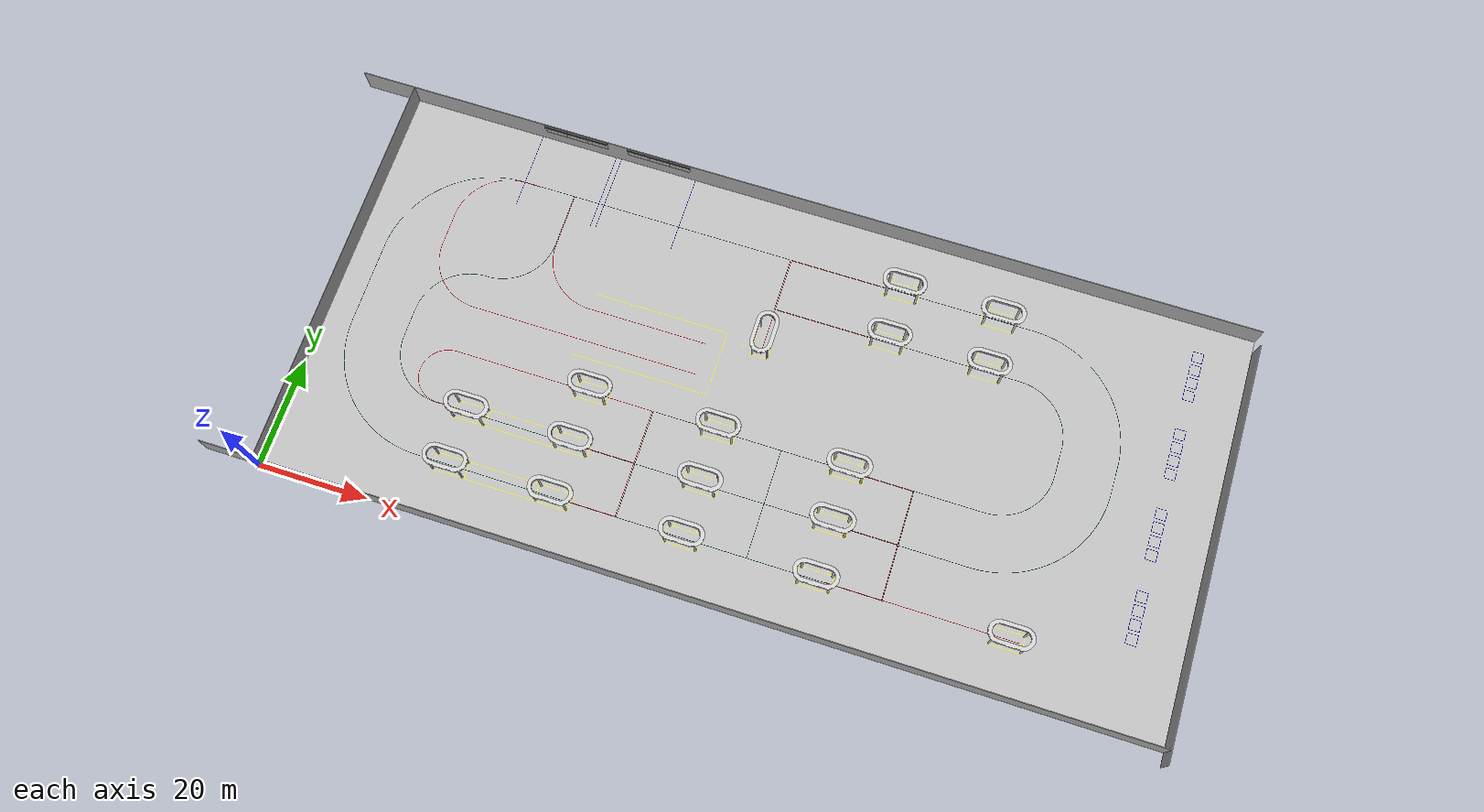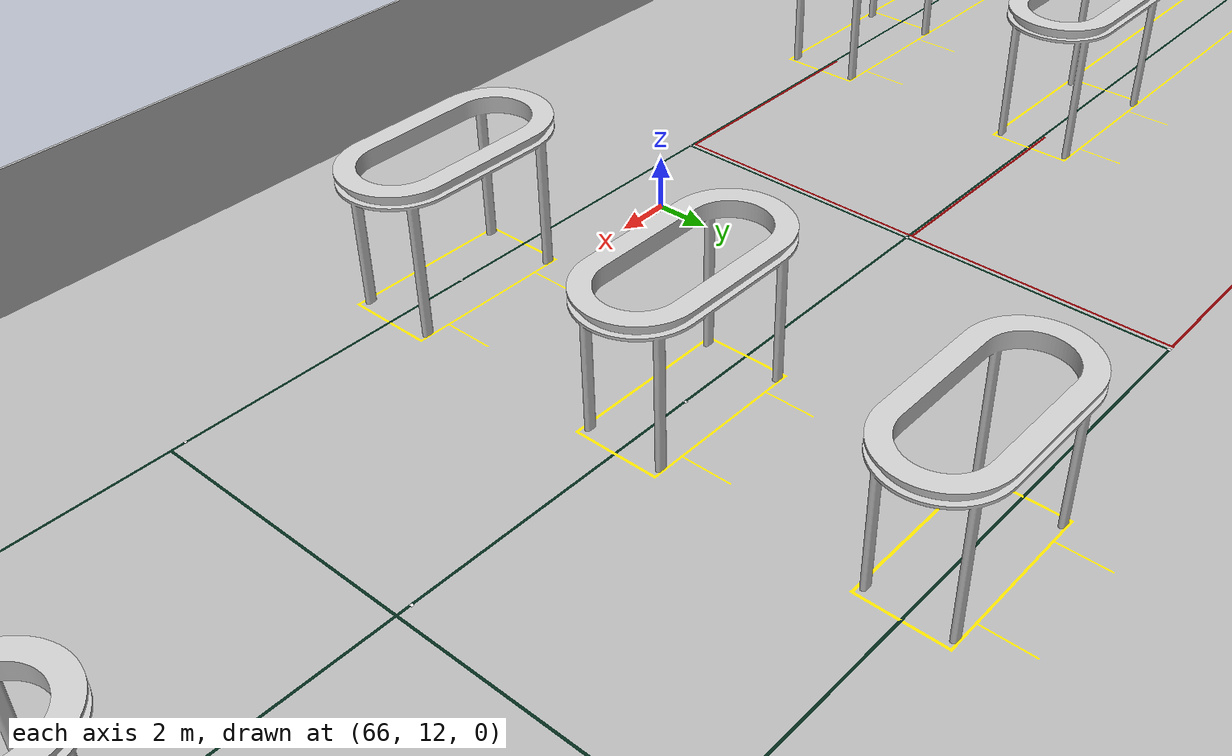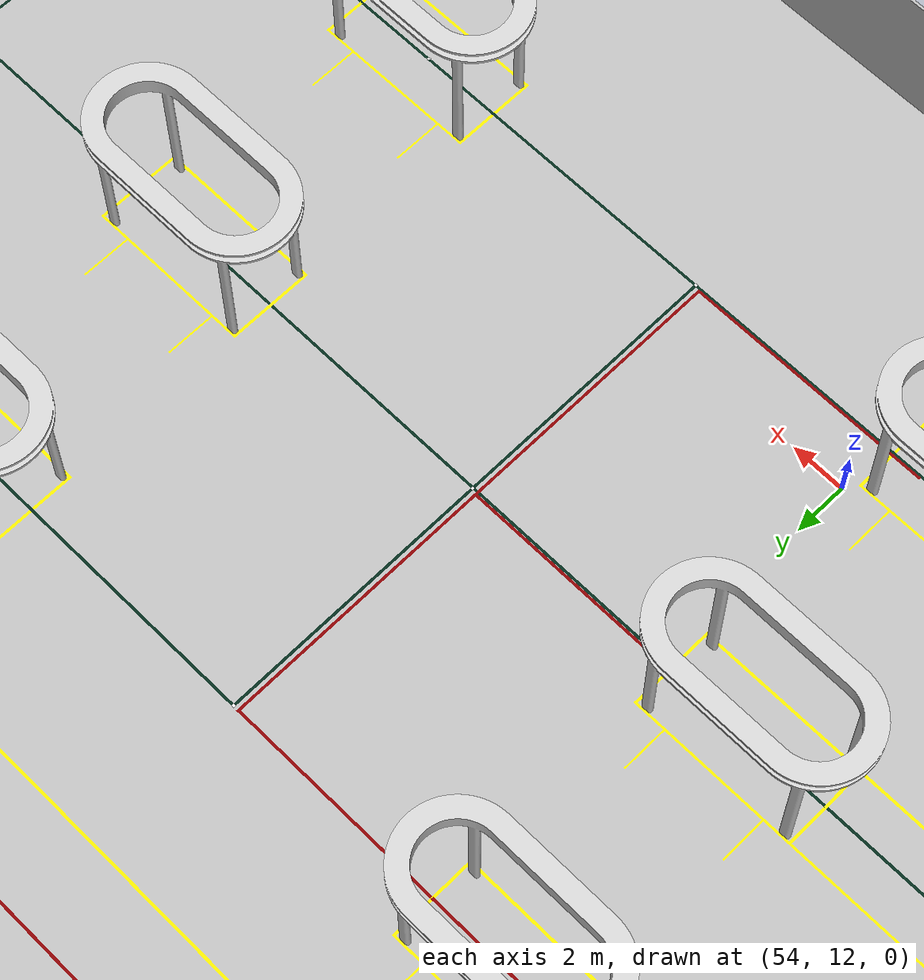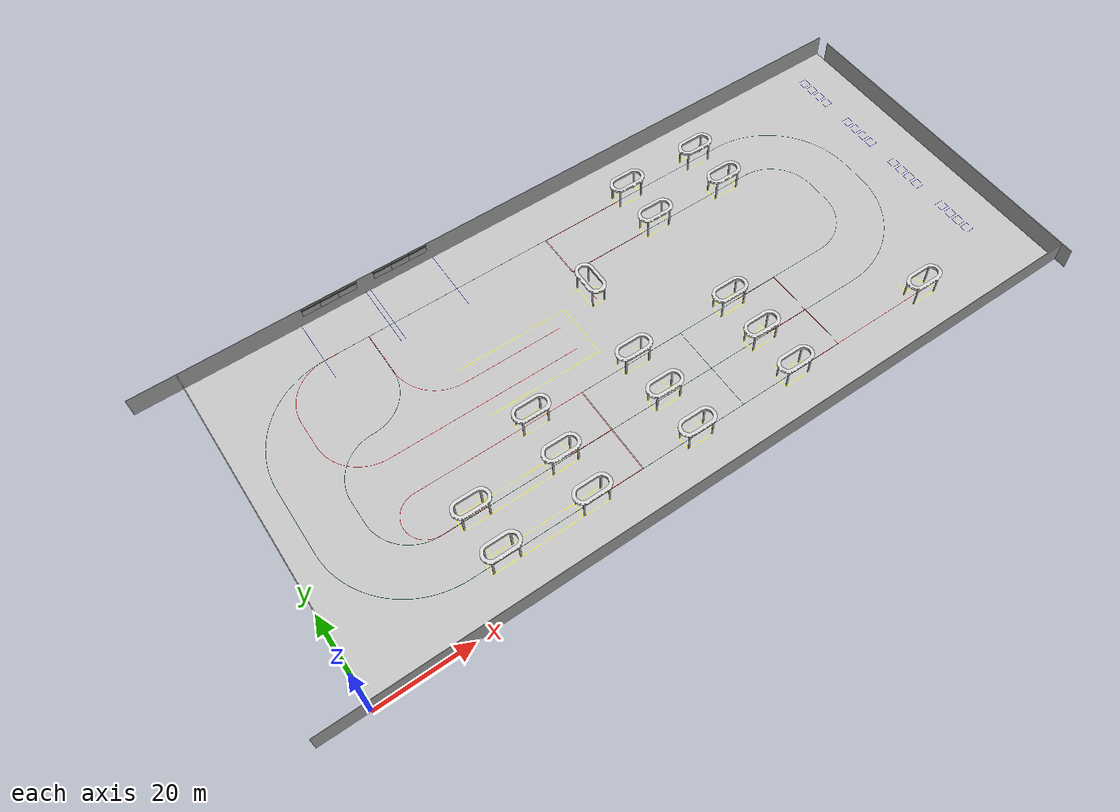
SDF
<sdf version="1.7">
 <world name="factory_ground">
  <gravity>0 0 -9.8</gravity>
  <physics name="default_physics" default="0" type="ode">
   <max_step_size>0.001</max_step_size>
   <real_time_factor>1</real_time_factor>
   <real_time_update_rate>1000</real_time_update_rate>
  </physics>
  <light name="sun" type="directional">
   <pose>0 0 10 0 -0 0</pose>
   <diffuse>0.8 0.8 0.8 1</diffuse>
   <specular>0.2 0.2 0.2 1</specular>
   <attenuation>
    <range>1000</range>
    <constant>0.9</constant>
    <linear>0.01</linear>
    <quadratic>0.001</quadratic>
   </attenuation>
   <direction>-0.5 0.1 -0.9</direction>
   <spot><inner_angle>0</inner_angle><outer_angle>0</outer_angle><falloff>0</falloff></spot>
  </light>
  <magnetic_field>6e-06 2.3e-05 -4.2e-05</magnetic_field>
  <atmosphere type="adiabatic"/>
  <scene><ambient>0.4 0.4 0.4 1</ambient><background>0.7 0.7 0.7 1</background><shadows>1</shadows></scene>
  <spherical_coordinates>
   <surface_model>EARTH_WGS84</surface_model>
   <latitude_deg>0</latitude_deg>
   <longitude_deg>0</longitude_deg>
   <elevation>0</elevation>
   <heading_deg>0</heading_deg>
  </spherical_coordinates>
  <model name="automobile_factory_Ground">
   <static>1</static>
   <pose>0 0 0 0.000523 -8.6e-05 -0</pose>
   <link name="link">
    <inertial>
     <mass>1000</mass>
     <inertia>
      <ixx>1.20008e+06</ixx>
      <ixy>0</ixy>
      <ixz>0</ixz>
      <iyy>8.33342e+06</iyy>
      <iyz>0</iyz>
      <izz>2.03333e+06</izz>
     </inertia>
    </inertial>
    <collision name="collision">
     <pose>80 37.5 0</pose>
     <geometry><plane><normal>0 0 1</normal><size>160 75</size></plane></geometry>
     <surface>
      <friction><ode><mu>100</mu><mu2>50</mu2><fdir1>0 0 0</fdir1><slip1>0</slip1><slip2>0</slip2></ode></friction>
     </surface>
    </collision>
    <visual name="visual">
     <geometry>
      <mesh><uri>model://automobile_factory_Ground/meshes/automobile_factory_Ground.dae</uri></mesh>
     </geometry>
     <meta><layer>1</layer></meta>
    </visual>
   </link>
   <static>1</static>
  </model>
  <model name="marker_1">
   <link name="marker">
    <visual name="visual">
     <geometry><box><size>0.1 0.1 1e-05</size></box></geometry>
     <material>
      <script>
       <uri>model://marker_1/materials/scripts</uri>
       <uri>model://marker_1/materials/textures</uri>
       <name>marker_material1</name>
      </script>
      <ambient>1 1 1 1</ambient>
      <diffuse>1 1 1 1</diffuse>
      <specular>0 0 0 1</specular>
      <emissive>1 1 1 0</emissive>
     </material>
    </visual>
    <collision name="collision"><geometry><box><size>0.1 0.1 1e-05</size></box></geometry></collision>
   </link>
   <link name="marker_pad">
    <pose relative_to="marker">0 0 -1e-05 0 -0 0</pose>
    <visual name="visual">
     <geometry><box><size>0.1 0.1 1e-05</size></box></geometry>
     <material>
      <lighting>1</lighting>
      <script><uri>file://media/materials/scripts/gazebo.material</uri><name>Gazebo/White</name></script>
      <ambient>0.3 0.3 0.3 1</ambient>
      <diffuse>0.7 0.7 0.7 1</diffuse>
      <specular>0.01 0.01 0.01 1</specular>
      <emissive>1 1 1 0</emissive>
     </material>
    </visual>
    <collision name="collision"><geometry><box><size>0.1 0.1 1e-05</size></box></geometry></collision>
   </link>
   <joint name="marker_JOINT_marker_pad" type="revolute">
    <parent>marker</parent>
    <child>marker_pad</child>
    <axis>
     <xyz>0 0 1</xyz>
     <limit><upper>0</upper><lower>0</lower></limit>
     <dynamics><spring_reference>0</spring_reference><spring_stiffness>0</spring_stiffness></dynamics>
    </axis>
   </joint>
   <static>1</static>
   <pose>32 10 0.046333 0 -0 0</pose>
  </model>
  <model name="marker_2">
   <link name="marker">
    <visual name="visual">
     <geometry><box><size>0.1 0.1 1e-05</size></box></geometry>
     <material>
      <script>
       <uri>model://marker_2/materials/scripts</uri>
       <uri>model://marker_2/materials/textures</uri>
       <name>marker_material2</name>
      </script>
      <ambient>1 1 1 1</ambient>
      <diffuse>1 1 1 1</diffuse>
      <specular>0 0 0 1</specular>
      <emissive>1 1 1 0</emissive>
     </material>
    </visual>
    <collision name="collision"><geometry><box><size>0.1 0.1 1e-05</size></box></geometry></collision>
   </link>
   <link name="marker_pad">
    <pose relative_to="marker">0 0 -1e-05 0 -0 0</pose>
    <visual name="visual">
     <geometry><box><size>0.1 0.1 1e-05</size></box></geometry>
     <material>
      <lighting>1</lighting>
      <script><uri>file://media/materials/scripts/gazebo.material</uri><name>Gazebo/White</name></script>
      <ambient>0.3 0.3 0.3 1</ambient>
      <diffuse>0.7 0.7 0.7 1</diffuse>
      <specular>0.01 0.01 0.01 1</specular>
      <emissive>1 1 1 0</emissive>
     </material>
    </visual>
    <collision name="collision"><geometry><box><size>0.1 0.1 1e-05</size></box></geometry></collision>
   </link>
   <joint name="marker_JOINT_marker_pad" type="revolute">
    <parent>marker</parent>
    <child>marker_pad</child>
    <axis>
     <xyz>0 0 1</xyz>
     <limit><upper>0</upper><lower>0</lower></limit>
     <dynamics><spring_reference>0</spring_reference><spring_stiffness>0</spring_stiffness></dynamics>
    </axis>
   </joint>
   <static>1</static>
   <pose>32 20 0.046333 0 -0 0</pose>
  </model>
  <model name="marker_3">
   <link name="marker">
    <visual name="visual">
     <geometry><box><size>0.1 0.1 1e-05</size></box></geometry>
     <material>
      <script>
       <uri>model://marker_3/materials/scripts</uri>
       <uri>model://marker_3/materials/textures</uri>
       <name>marker_material3</name>
      </script>
      <ambient>1 1 1 1</ambient>
      <diffuse>1 1 1 1</diffuse>
      <specular>0 0 0 1</specular>
      <emissive>1 1 1 0</emissive>
     </material>
    </visual>
    <collision name="collision"><geometry><box><size>0.1 0.1 1e-05</size></box></geometry></collision>
   </link>
   <link name="marker_pad">
    <pose relative_to="marker">0 0 -1e-05 0 -0 0</pose>
    <visual name="visual">
     <geometry><box><size>0.1 0.1 1e-05</size></box></geometry>
     <material>
      <lighting>1</lighting>
      <script><uri>file://media/materials/scripts/gazebo.material</uri><name>Gazebo/White</name></script>
      <ambient>0.3 0.3 0.3 1</ambient>
      <diffuse>0.7 0.7 0.7 1</diffuse>
      <specular>0.01 0.01 0.01 1</specular>
      <emissive>1 1 1 0</emissive>
     </material>
    </visual>
    <collision name="collision"><geometry><box><size>0.1 0.1 1e-05</size></box></geometry></collision>
   </link>
   <joint name="marker_JOINT_marker_pad" type="revolute">
    <parent>marker</parent>
    <child>marker_pad</child>
    <axis>
     <xyz>0 0 1</xyz>
     <limit><upper>0</upper><lower>0</lower></limit>
     <dynamics><spring_reference>0</spring_reference><spring_stiffness>0</spring_stiffness></dynamics>
    </axis>
   </joint>
   <static>1</static>
   <pose>50 10 0.046333 0 -0 0</pose>
  </model>
  <model name="marker_4">
   <link name="marker">
    <visual name="visual">
     <geometry><box><size>0.1 0.1 1e-05</size></box></geometry>
     <material>
      <script>
       <uri>model://marker_4/materials/scripts</uri>
       <uri>model://marker_4/materials/textures</uri>
       <name>marker_material4</name>
      </script>
      <ambient>1 1 1 1</ambient>
      <diffuse>1 1 1 1</diffuse>
      <specular>0 0 0 1</specular>
      <emissive>1 1 1 0</emissive>
     </material>
    </visual>
    <collision name="collision"><geometry><box><size>0.1 0.1 1e-05</size></box></geometry></collision>
   </link>
   <link name="marker_pad">
    <pose relative_to="marker">0 0 -1e-05 0 -0 0</pose>
    <visual name="visual">
     <geometry><box><size>0.1 0.1 1e-05</size></box></geometry>
     <material>
      <lighting>1</lighting>
      <script><uri>file://media/materials/scripts/gazebo.material</uri><name>Gazebo/White</name></script>
      <ambient>0.3 0.3 0.3 1</ambient>
      <diffuse>0.7 0.7 0.7 1</diffuse>
      <specular>0.01 0.01 0.01 1</specular>
      <emissive>1 1 1 0</emissive>
     </material>
    </visual>
    <collision name="collision"><geometry><box><size>0.1 0.1 1e-05</size></box></geometry></collision>
   </link>
   <joint name="marker_JOINT_marker_pad" type="revolute">
    <parent>marker</parent>
    <child>marker_pad</child>
    <axis>
     <xyz>0 0 1</xyz>
     <limit><upper>0</upper><lower>0</lower></limit>
     <dynamics><spring_reference>0</spring_reference><spring_stiffness>0</spring_stiffness></dynamics>
    </axis>
   </joint>
   <static>1</static>
   <pose>50 20 0.046333 0 -0 0</pose>
  </model>
  <model name="marker_5">
   <link name="marker">
    <visual name="visual">
     <geometry><box><size>0.1 0.1 1e-05</size></box></geometry>
     <material>
      <script>
       <uri>model://marker_5/materials/scripts</uri>
       <uri>model://marker_5/materials/textures</uri>
       <name>marker_material5</name>
      </script>
      <ambient>1 1 1 1</ambient>
      <diffuse>1 1 1 1</diffuse>
      <specular>0 0 0 1</specular>
      <emissive>1 1 1 0</emissive>
     </material>
    </visual>
    <collision name="collision"><geometry><box><size>0.1 0.1 1e-05</size></box></geometry></collision>
   </link>
   <link name="marker_pad">
    <pose relative_to="marker">0 0 -1e-05 0 -0 0</pose>
    <visual name="visual">
     <geometry><box><size>0.1 0.1 1e-05</size></box></geometry>
     <material>
      <lighting>1</lighting>
      <script><uri>file://media/materials/scripts/gazebo.material</uri><name>Gazebo/White</name></script>
      <ambient>0.3 0.3 0.3 1</ambient>
      <diffuse>0.7 0.7 0.7 1</diffuse>
      <specular>0.01 0.01 0.01 1</specular>
      <emissive>1 1 1 0</emissive>
     </material>
    </visual>
    <collision name="collision"><geometry><box><size>0.1 0.1 1e-05</size></box></geometry></collision>
   </link>
   <joint name="marker_JOINT_marker_pad" type="revolute">
    <parent>marker</parent>
    <child>marker_pad</child>
    <axis>
     <xyz>0 0 1</xyz>
     <limit><upper>0</upper><lower>0</lower></limit>
     <dynamics><spring_reference>0</spring_reference><spring_stiffness>0</spring_stiffness></dynamics>
    </axis>
   </joint>
   <static>1</static>
   <pose>50 30 0.046333 0 -0 0</pose>
  </model>
  <model name="marker_6">
   <link name="marker">
    <visual name="visual">
     <geometry><box><size>0.1 0.1 1e-05</size></box></geometry>
     <material>
      <script>
       <uri>model://marker_6/materials/scripts</uri>
       <uri>model://marker_6/materials/textures</uri>
       <name>marker_material6</name>
      </script>
      <ambient>1 1 1 1</ambient>
      <diffuse>1 1 1 1</diffuse>
      <specular>0 0 0 1</specular>
      <emissive>1 1 1 0</emissive>
     </material>
    </visual>
    <collision name="collision"><geometry><box><size>0.1 0.1 1e-05</size></box></geometry></collision>
   </link>
   <link name="marker_pad">
    <pose relative_to="marker">0 0 -1e-05 0 -0 0</pose>
    <visual name="visual">
     <geometry><box><size>0.1 0.1 1e-05</size></box></geometry>
     <material>
      <lighting>1</lighting>
      <script><uri>file://media/materials/scripts/gazebo.material</uri><name>Gazebo/White</name></script>
      <ambient>0.3 0.3 0.3 1</ambient>
      <diffuse>0.7 0.7 0.7 1</diffuse>
      <specular>0.01 0.01 0.01 1</specular>
      <emissive>1 1 1 0</emissive>
     </material>
    </visual>
    <collision name="collision"><geometry><box><size>0.1 0.1 1e-05</size></box></geometry></collision>
   </link>
   <joint name="marker_JOINT_marker_pad" type="revolute">
    <parent>marker</parent>
    <child>marker_pad</child>
    <axis>
     <xyz>0 0 1</xyz>
     <limit><upper>0</upper><lower>0</lower></limit>
     <dynamics><spring_reference>0</spring_reference><spring_stiffness>0</spring_stiffness></dynamics>
    </axis>
   </joint>
   <static>1</static>
   <pose>62 10 0.046333 0 -0 0</pose>
  </model>
  <model name="marker_7">
   <link name="marker">
    <visual name="visual">
     <geometry><box><size>0.1 0.1 1e-05</size></box></geometry>
     <material>
      <script>
       <uri>model://marker_7/materials/scripts</uri>
       <uri>model://marker_7/materials/textures</uri>
       <name>marker_material7</name>
      </script>
      <ambient>1 1 1 1</ambient>
      <diffuse>1 1 1 1</diffuse>
      <specular>0 0 0 1</specular>
      <emissive>1 1 1 0</emissive>
     </material>
    </visual>
    <collision name="collision"><geometry><box><size>0.1 0.1 1e-05</size></box></geometry></collision>
   </link>
   <link name="marker_pad">
    <pose relative_to="marker">0 0 -1e-05 0 -0 0</pose>
    <visual name="visual">
     <geometry><box><size>0.1 0.1 1e-05</size></box></geometry>
     <material>
      <lighting>1</lighting>
      <script><uri>file://media/materials/scripts/gazebo.material</uri><name>Gazebo/White</name></script>
      <ambient>0.3 0.3 0.3 1</ambient>
      <diffuse>0.7 0.7 0.7 1</diffuse>
      <specular>0.01 0.01 0.01 1</specular>
      <emissive>1 1 1 0</emissive>
     </material>
    </visual>
    <collision name="collision"><geometry><box><size>0.1 0.1 1e-05</size></box></geometry></collision>
   </link>
   <joint name="marker_JOINT_marker_pad" type="revolute">
    <parent>marker</parent>
    <child>marker_pad</child>
    <axis>
     <xyz>0 0 1</xyz>
     <limit><upper>0</upper><lower>0</lower></limit>
     <dynamics><spring_reference>0</spring_reference><spring_stiffness>0</spring_stiffness></dynamics>
    </axis>
   </joint>
   <static>1</static>
   <pose>62 20 0.046333 0 -0 0</pose>
  </model>
  <model name="marker_8">
   <link name="marker">
    <visual name="visual">
     <geometry><box><size>0.1 0.1 1e-05</size></box></geometry>
     <material>
      <script>
       <uri>model://marker_8/materials/scripts</uri>
       <uri>model://marker_8/materials/textures</uri>
       <name>marker_material8</name>
      </script>
      <ambient>1 1 1 1</ambient>
      <diffuse>1 1 1 1</diffuse>
      <specular>0 0 0 1</specular>
      <emissive>1 1 1 0</emissive>
     </material>
    </visual>
    <collision name="collision"><geometry><box><size>0.1 0.1 1e-05</size></box></geometry></collision>
   </link>
   <link name="marker_pad">
    <pose relative_to="marker">0 0 -1e-05 0 -0 0</pose>
    <visual name="visual">
     <geometry><box><size>0.1 0.1 1e-05</size></box></geometry>
     <material>
      <lighting>1</lighting>
      <script><uri>file://media/materials/scripts/gazebo.material</uri><name>Gazebo/White</name></script>
      <ambient>0.3 0.3 0.3 1</ambient>
      <diffuse>0.7 0.7 0.7 1</diffuse>
      <specular>0.01 0.01 0.01 1</specular>
      <emissive>1 1 1 0</emissive>
     </material>
    </visual>
    <collision name="collision"><geometry><box><size>0.1 0.1 1e-05</size></box></geometry></collision>
   </link>
   <joint name="marker_JOINT_marker_pad" type="revolute">
    <parent>marker</parent>
    <child>marker_pad</child>
    <axis>
     <xyz>0 0 1</xyz>
     <limit><upper>0</upper><lower>0</lower></limit>
     <dynamics><spring_reference>0</spring_reference><spring_stiffness>0</spring_stiffness></dynamics>
    </axis>
   </joint>
   <static>1</static>
   <pose>62 30 0.046333 0 -0 0</pose>
  </model>
  <model name="marker_9">
   <link name="marker">
    <visual name="visual">
     <geometry><box><size>0.1 0.1 1e-05</size></box></geometry>
     <material>
      <script>
       <uri>model://marker_9/materials/scripts</uri>
       <uri>model://marker_9/materials/textures</uri>
       <name>marker_material9</name>
      </script>
      <ambient>1 1 1 1</ambient>
      <diffuse>1 1 1 1</diffuse>
      <specular>0 0 0 1</specular>
      <emissive>1 1 1 0</emissive>
     </material>
    </visual>
    <collision name="collision"><geometry><box><size>0.1 0.1 1e-05</size></box></geometry></collision>
   </link>
   <link name="marker_pad">
    <pose relative_to="marker">0 0 -1e-05 0 -0 0</pose>
    <visual name="visual">
     <geometry><box><size>0.1 0.1 1e-05</size></box></geometry>
     <material>
      <lighting>1</lighting>
      <script><uri>file://media/materials/scripts/gazebo.material</uri><name>Gazebo/White</name></script>
      <ambient>0.3 0.3 0.3 1</ambient>
      <diffuse>0.7 0.7 0.7 1</diffuse>
      <specular>0.01 0.01 0.01 1</specular>
      <emissive>1 1 1 0</emissive>
     </material>
    </visual>
    <collision name="collision"><geometry><box><size>0.1 0.1 1e-05</size></box></geometry></collision>
   </link>
   <joint name="marker_JOINT_marker_pad" type="revolute">
    <parent>marker</parent>
    <child>marker_pad</child>
    <axis>
     <xyz>0 0 1</xyz>
     <limit><upper>0</upper><lower>0</lower></limit>
     <dynamics><spring_reference>0</spring_reference><spring_stiffness>0</spring_stiffness></dynamics>
    </axis>
   </joint>
   <static>1</static>
   <pose>74 10 0.046333 0 -0 0</pose>
  </model>
  <model name="marker_10">
   <link name="marker">
    <visual name="visual">
     <geometry><box><size>0.1 0.1 1e-05</size></box></geometry>
     <material>
      <script>
       <uri>model://marker_10/materials/scripts</uri>
       <uri>model://marker_10/materials/textures</uri>
       <name>marker_material10</name>
      </script>
      <ambient>1 1 1 1</ambient>
      <diffuse>1 1 1 1</diffuse>
      <specular>0 0 0 1</specular>
      <emissive>1 1 1 0</emissive>
     </material>
    </visual>
    <collision name="collision"><geometry><box><size>0.1 0.1 1e-05</size></box></geometry></collision>
   </link>
   <link name="marker_pad">
    <pose relative_to="marker">0 0 -1e-05 0 -0 0</pose>
    <visual name="visual">
     <geometry><box><size>0.1 0.1 1e-05</size></box></geometry>
     <material>
      <lighting>1</lighting>
      <script><uri>file://media/materials/scripts/gazebo.material</uri><name>Gazebo/White</name></script>
      <ambient>0.3 0.3 0.3 1</ambient>
      <diffuse>0.7 0.7 0.7 1</diffuse>
      <specular>0.01 0.01 0.01 1</specular>
      <emissive>1 1 1 0</emissive>
     </material>
    </visual>
    <collision name="collision"><geometry><box><size>0.1 0.1 1e-05</size></box></geometry></collision>
   </link>
   <joint name="marker_JOINT_marker_pad" type="revolute">
    <parent>marker</parent>
    <child>marker_pad</child>
    <axis>
     <xyz>0 0 1</xyz>
     <limit><upper>0</upper><lower>0</lower></limit>
     <dynamics><spring_reference>0</spring_reference><spring_stiffness>0</spring_stiffness></dynamics>
    </axis>
   </joint>
   <static>1</static>
   <pose>74 20 0.046333 0 -0 0</pose>
  </model>
  <model name="marker_11">
   <link name="marker">
    <visual name="visual">
     <geometry><box><size>0.1 0.1 1e-05</size></box></geometry>
     <material>
      <script>
       <uri>model://marker_11/materials/scripts</uri>
       <uri>model://marker_11/materials/textures</uri>
       <name>marker_material11</name>
      </script>
      <ambient>1 1 1 1</ambient>
      <diffuse>1 1 1 1</diffuse>
      <specular>0 0 0 1</specular>
      <emissive>1 1 1 0</emissive>
     </material>
    </visual>
    <collision name="collision"><geometry><box><size>0.1 0.1 1e-05</size></box></geometry></collision>
   </link>
   <link name="marker_pad">
    <pose relative_to="marker">0 0 -1e-05 0 -0 0</pose>
    <visual name="visual">
     <geometry><box><size>0.1 0.1 1e-05</size></box></geometry>
     <material>
      <lighting>1</lighting>
      <script><uri>file://media/materials/scripts/gazebo.material</uri><name>Gazebo/White</name></script>
      <ambient>0.3 0.3 0.3 1</ambient>
      <diffuse>0.7 0.7 0.7 1</diffuse>
      <specular>0.01 0.01 0.01 1</specular>
      <emissive>1 1 1 0</emissive>
     </material>
    </visual>
    <collision name="collision"><geometry><box><size>0.1 0.1 1e-05</size></box></geometry></collision>
   </link>
   <joint name="marker_JOINT_marker_pad" type="revolute">
    <parent>marker</parent>
    <child>marker_pad</child>
    <axis>
     <xyz>0 0 1</xyz>
     <limit><upper>0</upper><lower>0</lower></limit>
     <dynamics><spring_reference>0</spring_reference><spring_stiffness>0</spring_stiffness></dynamics>
    </axis>
   </joint>
   <static>1</static>
   <pose>74 30 0.046333 0 -0 0</pose>
  </model>
  <model name="marker_12">
   <link name="marker">
    <visual name="visual">
     <geometry><box><size>0.1 0.1 1e-05</size></box></geometry>
     <material>
      <script>
       <uri>model://marker_12/materials/scripts</uri>
       <uri>model://marker_12/materials/textures</uri>
       <name>marker_material12</name>
      </script>
      <ambient>1 1 1 1</ambient>
      <diffuse>1 1 1 1</diffuse>
      <specular>0 0 0 1</specular>
      <emissive>1 1 1 0</emissive>
     </material>
    </visual>
    <collision name="collision"><geometry><box><size>0.1 0.1 1e-05</size></box></geometry></collision>
   </link>
   <link name="marker_pad">
    <pose relative_to="marker">0 0 -1e-05 0 -0 0</pose>
    <visual name="visual">
     <geometry><box><size>0.1 0.1 1e-05</size></box></geometry>
     <material>
      <lighting>1</lighting>
      <script><uri>file://media/materials/scripts/gazebo.material</uri><name>Gazebo/White</name></script>
      <ambient>0.3 0.3 0.3 1</ambient>
      <diffuse>0.7 0.7 0.7 1</diffuse>
      <specular>0.01 0.01 0.01 1</specular>
      <emissive>1 1 1 0</emissive>
     </material>
    </visual>
    <collision name="collision"><geometry><box><size>0.1 0.1 1e-05</size></box></geometry></collision>
   </link>
   <joint name="marker_JOINT_marker_pad" type="revolute">
    <parent>marker</parent>
    <child>marker_pad</child>
    <axis>
     <xyz>0 0 1</xyz>
     <limit><upper>0</upper><lower>0</lower></limit>
     <dynamics><spring_reference>0</spring_reference><spring_stiffness>0</spring_stiffness></dynamics>
    </axis>
   </joint>
   <static>1</static>
   <pose>85 10 0.046333 0 -0 0</pose>
  </model>
  <model name="marker_13">
   <link name="marker">
    <visual name="visual">
     <geometry><box><size>0.1 0.1 1e-05</size></box></geometry>
     <material>
      <script>
       <uri>model://marker_13/materials/scripts</uri>
       <uri>model://marker_13/materials/textures</uri>
       <name>marker_material13</name>
      </script>
      <ambient>1 1 1 1</ambient>
      <diffuse>1 1 1 1</diffuse>
      <specular>0 0 0 1</specular>
      <emissive>1 1 1 0</emissive>
     </material>
    </visual>
    <collision name="collision"><geometry><box><size>0.1 0.1 1e-05</size></box></geometry></collision>
   </link>
   <link name="marker_pad">
    <pose relative_to="marker">0 0 -1e-05 0 -0 0</pose>
    <visual name="visual">
     <geometry><box><size>0.1 0.1 1e-05</size></box></geometry>
     <material>
      <lighting>1</lighting>
      <script><uri>file://media/materials/scripts/gazebo.material</uri><name>Gazebo/White</name></script>
      <ambient>0.3 0.3 0.3 1</ambient>
      <diffuse>0.7 0.7 0.7 1</diffuse>
      <specular>0.01 0.01 0.01 1</specular>
      <emissive>1 1 1 0</emissive>
     </material>
    </visual>
    <collision name="collision"><geometry><box><size>0.1 0.1 1e-05</size></box></geometry></collision>
   </link>
   <joint name="marker_JOINT_marker_pad" type="revolute">
    <parent>marker</parent>
    <child>marker_pad</child>
    <axis>
     <xyz>0 0 1</xyz>
     <limit><upper>0</upper><lower>0</lower></limit>
     <dynamics><spring_reference>0</spring_reference><spring_stiffness>0</spring_stiffness></dynamics>
    </axis>
   </joint>
   <static>1</static>
   <pose>85 20 0.046333 0 -0 0</pose>
  </model>
  <model name="marker_14">
   <link name="marker">
    <visual name="visual">
     <geometry><box><size>0.1 0.1 1e-05</size></box></geometry>
     <material>
      <script>
       <uri>model://marker_14/materials/scripts</uri>
       <uri>model://marker_14/materials/textures</uri>
       <name>marker_material14</name>
      </script>
      <ambient>1 1 1 1</ambient>
      <diffuse>1 1 1 1</diffuse>
      <specular>0 0 0 1</specular>
      <emissive>1 1 1 0</emissive>
     </material>
    </visual>
    <collision name="collision"><geometry><box><size>0.1 0.1 1e-05</size></box></geometry></collision>
   </link>
   <link name="marker_pad">
    <pose relative_to="marker">0 0 -1e-05 0 -0 0</pose>
    <visual name="visual">
     <geometry><box><size>0.1 0.1 1e-05</size></box></geometry>
     <material>
      <lighting>1</lighting>
      <script><uri>file://media/materials/scripts/gazebo.material</uri><name>Gazebo/White</name></script>
      <ambient>0.3 0.3 0.3 1</ambient>
      <diffuse>0.7 0.7 0.7 1</diffuse>
      <specular>0.01 0.01 0.01 1</specular>
      <emissive>1 1 1 0</emissive>
     </material>
    </visual>
    <collision name="collision"><geometry><box><size>0.1 0.1 1e-05</size></box></geometry></collision>
   </link>
   <joint name="marker_JOINT_marker_pad" type="revolute">
    <parent>marker</parent>
    <child>marker_pad</child>
    <axis>
     <xyz>0 0 1</xyz>
     <limit><upper>0</upper><lower>0</lower></limit>
     <dynamics><spring_reference>0</spring_reference><spring_stiffness>0</spring_stiffness></dynamics>
    </axis>
   </joint>
   <static>1</static>
   <pose>85 30 0.046333 0 -0 0</pose>
  </model>
  <model name="marker_15">
   <link name="marker">
    <visual name="visual">
     <geometry><box><size>0.1 0.1 1e-05</size></box></geometry>
     <material>
      <script>
       <uri>model://marker_15/materials/scripts</uri>
       <uri>model://marker_15/materials/textures</uri>
       <name>marker_material15</name>
      </script>
      <ambient>1 1 1 1</ambient>
      <diffuse>1 1 1 1</diffuse>
      <specular>0 0 0 1</specular>
      <emissive>1 1 1 0</emissive>
     </material>
    </visual>
    <collision name="collision"><geometry><box><size>0.1 0.1 1e-05</size></box></geometry></collision>
   </link>
   <link name="marker_pad">
    <pose relative_to="marker">0 0 -1e-05 0 -0 0</pose>
    <visual name="visual">
     <geometry><box><size>0.1 0.1 1e-05</size></box></geometry>
     <material>
      <lighting>1</lighting>
      <script><uri>file://media/materials/scripts/gazebo.material</uri><name>Gazebo/White</name></script>
      <ambient>0.3 0.3 0.3 1</ambient>
      <diffuse>0.7 0.7 0.7 1</diffuse>
      <specular>0.01 0.01 0.01 1</specular>
      <emissive>1 1 1 0</emissive>
     </material>
    </visual>
    <collision name="collision"><geometry><box><size>0.1 0.1 1e-05</size></box></geometry></collision>
   </link>
   <joint name="marker_JOINT_marker_pad" type="revolute">
    <parent>marker</parent>
    <child>marker_pad</child>
    <axis>
     <xyz>0 0 1</xyz>
     <limit><upper>0</upper><lower>0</lower></limit>
     <dynamics><spring_reference>0</spring_reference><spring_stiffness>0</spring_stiffness></dynamics>
    </axis>
   </joint>
   <static>1</static>
   <pose>97 10 0.046333 0 -0 0</pose>
  </model>
  <model name="marker_16">
   <link name="marker">
    <visual name="visual">
     <geometry><box><size>0.1 0.1 1e-05</size></box></geometry>
     <material>
      <script>
       <uri>model://marker_16/materials/scripts</uri>
       <uri>model://marker_16/materials/textures</uri>
       <name>marker_material16</name>
      </script>
      <ambient>1 1 1 1</ambient>
      <diffuse>1 1 1 1</diffuse>
      <specular>0 0 0 1</specular>
      <emissive>1 1 1 0</emissive>
     </material>
    </visual>
    <collision name="collision"><geometry><box><size>0.1 0.1 1e-05</size></box></geometry></collision>
   </link>
   <link name="marker_pad">
    <pose relative_to="marker">0 0 -1e-05 0 -0 0</pose>
    <visual name="visual">
     <geometry><box><size>0.1 0.1 1e-05</size></box></geometry>
     <material>
      <lighting>1</lighting>
      <script><uri>file://media/materials/scripts/gazebo.material</uri><name>Gazebo/White</name></script>
      <ambient>0.3 0.3 0.3 1</ambient>
      <diffuse>0.7 0.7 0.7 1</diffuse>
      <specular>0.01 0.01 0.01 1</specular>
      <emissive>1 1 1 0</emissive>
     </material>
    </visual>
    <collision name="collision"><geometry><box><size>0.1 0.1 1e-05</size></box></geometry></collision>
   </link>
   <joint name="marker_JOINT_marker_pad" type="revolute">
    <parent>marker</parent>
    <child>marker_pad</child>
    <axis>
     <xyz>0 0 1</xyz>
     <limit><upper>0</upper><lower>0</lower></limit>
     <dynamics><spring_reference>0</spring_reference><spring_stiffness>0</spring_stiffness></dynamics>
    </axis>
   </joint>
   <static>1</static>
   <pose>97 20 0.046333 0 -0 0</pose>
  </model>
  <model name="marker_17">
   <link name="marker">
    <visual name="visual">
     <geometry><box><size>0.1 0.1 1e-05</size></box></geometry>
     <material>
      <script>
       <uri>model://marker_17/materials/scripts</uri>
       <uri>model://marker_17/materials/textures</uri>
       <name>marker_material17</name>
      </script>
      <ambient>1 1 1 1</ambient>
      <diffuse>1 1 1 1</diffuse>
      <specular>0 0 0 1</specular>
      <emissive>1 1 1 0</emissive>
     </material>
    </visual>
    <collision name="collision"><geometry><box><size>0.1 0.1 1e-05</size></box></geometry></collision>
   </link>
   <link name="marker_pad">
    <pose relative_to="marker">0 0 -1e-05 0 -0 0</pose>
    <visual name="visual">
     <geometry><box><size>0.1 0.1 1e-05</size></box></geometry>
     <material>
      <lighting>1</lighting>
      <script><uri>file://media/materials/scripts/gazebo.material</uri><name>Gazebo/White</name></script>
      <ambient>0.3 0.3 0.3 1</ambient>
      <diffuse>0.7 0.7 0.7 1</diffuse>
      <specular>0.01 0.01 0.01 1</specular>
      <emissive>1 1 1 0</emissive>
     </material>
    </visual>
    <collision name="collision"><geometry><box><size>0.1 0.1 1e-05</size></box></geometry></collision>
   </link>
   <joint name="marker_JOINT_marker_pad" type="revolute">
    <parent>marker</parent>
    <child>marker_pad</child>
    <axis>
     <xyz>0 0 1</xyz>
     <limit><upper>0</upper><lower>0</lower></limit>
     <dynamics><spring_reference>0</spring_reference><spring_stiffness>0</spring_stiffness></dynamics>
    </axis>
   </joint>
   <static>1</static>
   <pose>97 30 0.046333 0 -0 0</pose>
  </model>
  <model name="marker_18">
   <link name="marker">
    <visual name="visual">
     <geometry><box><size>0.1 0.1 1e-05</size></box></geometry>
     <material>
      <script>
       <uri>model://marker_18/materials/scripts</uri>
       <uri>model://marker_18/materials/textures</uri>
       <name>marker_material18</name>
      </script>
      <ambient>1 1 1 1</ambient>
      <diffuse>1 1 1 1</diffuse>
      <specular>0 0 0 1</specular>
      <emissive>1 1 1 0</emissive>
     </material>
    </visual>
    <collision name="collision"><geometry><box><size>0.1 0.1 1e-05</size></box></geometry></collision>
   </link>
   <link name="marker_pad">
    <pose relative_to="marker">0 0 -1e-05 0 -0 0</pose>
    <visual name="visual">
     <geometry><box><size>0.1 0.1 1e-05</size></box></geometry>
     <material>
      <lighting>1</lighting>
      <script><uri>file://media/materials/scripts/gazebo.material</uri><name>Gazebo/White</name></script>
      <ambient>0.3 0.3 0.3 1</ambient>
      <diffuse>0.7 0.7 0.7 1</diffuse>
      <specular>0.01 0.01 0.01 1</specular>
      <emissive>1 1 1 0</emissive>
     </material>
    </visual>
    <collision name="collision"><geometry><box><size>0.1 0.1 1e-05</size></box></geometry></collision>
   </link>
   <joint name="marker_JOINT_marker_pad" type="revolute">
    <parent>marker</parent>
    <child>marker_pad</child>
    <axis>
     <xyz>0 0 1</xyz>
     <limit><upper>0</upper><lower>0</lower></limit>
     <dynamics><spring_reference>0</spring_reference><spring_stiffness>0</spring_stiffness></dynamics>
    </axis>
   </joint>
   <static>1</static>
   <pose>109.5 10 0.046333 0 -0 0</pose>
  </model>
  <model name="marker_19">
   <link name="marker">
    <visual name="visual">
     <geometry><box><size>0.1 0.1 1e-05</size></box></geometry>
     <material>
      <script>
       <uri>model://marker_19/materials/scripts</uri>
       <uri>model://marker_19/materials/textures</uri>
       <name>marker_material19</name>
      </script>
      <ambient>1 1 1 1</ambient>
      <diffuse>1 1 1 1</diffuse>
      <specular>0 0 0 1</specular>
      <emissive>1 1 1 0</emissive>
     </material>
    </visual>
    <collision name="collision"><geometry><box><size>0.1 0.1 1e-05</size></box></geometry></collision>
   </link>
   <link name="marker_pad">
    <pose relative_to="marker">0 0 -1e-05 0 -0 0</pose>
    <visual name="visual">
     <geometry><box><size>0.1 0.1 1e-05</size></box></geometry>
     <material>
      <lighting>1</lighting>
      <script><uri>file://media/materials/scripts/gazebo.material</uri><name>Gazebo/White</name></script>
      <ambient>0.3 0.3 0.3 1</ambient>
      <diffuse>0.7 0.7 0.7 1</diffuse>
      <specular>0.01 0.01 0.01 1</specular>
      <emissive>1 1 1 0</emissive>
     </material>
    </visual>
    <collision name="collision"><geometry><box><size>0.1 0.1 1e-05</size></box></geometry></collision>
   </link>
   <joint name="marker_JOINT_marker_pad" type="revolute">
    <parent>marker</parent>
    <child>marker_pad</child>
    <axis>
     <xyz>0 0 1</xyz>
     <limit><upper>0</upper><lower>0</lower></limit>
     <dynamics><spring_reference>0</spring_reference><spring_stiffness>0</spring_stiffness></dynamics>
    </axis>
   </joint>
   <static>1</static>
   <pose>109.5 20 0.046333 0 -0 0</pose>
  </model>
  <model name="marker_20">
   <link name="marker">
    <visual name="visual">
     <geometry><box><size>0.1 0.1 1e-05</size></box></geometry>
     <material>
      <script>
       <uri>model://marker_20/materials/scripts</uri>
       <uri>model://marker_20/materials/textures</uri>
       <name>marker_material20</name>
      </script>
      <ambient>1 1 1 1</ambient>
      <diffuse>1 1 1 1</diffuse>
      <specular>0 0 0 1</specular>
      <emissive>1 1 1 0</emissive>
     </material>
    </visual>
    <collision name="collision"><geometry><box><size>0.1 0.1 1e-05</size></box></geometry></collision>
   </link>
   <link name="marker_pad">
    <pose relative_to="marker">0 0 -1e-05 0 -0 0</pose>
    <visual name="visual">
     <geometry><box><size>0.1 0.1 1e-05</size></box></geometry>
     <material>
      <lighting>1</lighting>
      <script><uri>file://media/materials/scripts/gazebo.material</uri><name>Gazebo/White</name></script>
      <ambient>0.3 0.3 0.3 1</ambient>
      <diffuse>0.7 0.7 0.7 1</diffuse>
      <specular>0.01 0.01 0.01 1</specular>
      <emissive>1 1 1 0</emissive>
     </material>
    </visual>
    <collision name="collision"><geometry><box><size>0.1 0.1 1e-05</size></box></geometry></collision>
   </link>
   <joint name="marker_JOINT_marker_pad" type="revolute">
    <parent>marker</parent>
    <child>marker_pad</child>
    <axis>
     <xyz>0 0 1</xyz>
     <limit><upper>0</upper><lower>0</lower></limit>
     <dynamics><spring_reference>0</spring_reference><spring_stiffness>0</spring_stiffness></dynamics>
    </axis>
   </joint>
   <static>1</static>
   <pose>109.5 30 0.046333 0 -0 0</pose>
  </model>
  <model name="marker_21">
   <link name="marker">
    <visual name="visual">
     <geometry><box><size>0.1 0.1 1e-05</size></box></geometry>
     <material>
      <script>
       <uri>model://marker_21/materials/scripts</uri>
       <uri>model://marker_21/materials/textures</uri>
       <name>marker_material21</name>
      </script>
      <ambient>1 1 1 1</ambient>
      <diffuse>1 1 1 1</diffuse>
      <specular>0 0 0 1</specular>
      <emissive>1 1 1 0</emissive>
     </material>
    </visual>
    <collision name="collision"><geometry><box><size>0.1 0.1 1e-05</size></box></geometry></collision>
   </link>
   <link name="marker_pad">
    <pose relative_to="marker">0 0 -1e-05 0 -0 0</pose>
    <visual name="visual">
     <geometry><box><size>0.1 0.1 1e-05</size></box></geometry>
     <material>
      <lighting>1</lighting>
      <script><uri>file://media/materials/scripts/gazebo.material</uri><name>Gazebo/White</name></script>
      <ambient>0.3 0.3 0.3 1</ambient>
      <diffuse>0.7 0.7 0.7 1</diffuse>
      <specular>0.01 0.01 0.01 1</specular>
      <emissive>1 1 1 0</emissive>
     </material>
    </visual>
    <collision name="collision"><geometry><box><size>0.1 0.1 1e-05</size></box></geometry></collision>
   </link>
   <joint name="marker_JOINT_marker_pad" type="revolute">
    <parent>marker</parent>
    <child>marker_pad</child>
    <axis>
     <xyz>0 0 1</xyz>
     <limit><upper>0</upper><lower>0</lower></limit>
     <dynamics><spring_reference>0</spring_reference><spring_stiffness>0</spring_stiffness></dynamics>
    </axis>
   </joint>
   <static>1</static>
   <pose>131.233 10 0.046333 0 -0 0</pose>
  </model>
  <model name="marker_22">
   <link name="marker">
    <visual name="visual">
     <geometry><box><size>0.1 0.1 1e-05</size></box></geometry>
     <material>
      <script>
       <uri>model://marker_22/materials/scripts</uri>
       <uri>model://marker_22/materials/textures</uri>
       <name>marker_material22</name>
      </script>
      <ambient>1 1 1 1</ambient>
      <diffuse>1 1 1 1</diffuse>
      <specular>0 0 0 1</specular>
      <emissive>1 1 1 0</emissive>
     </material>
    </visual>
    <collision name="collision"><geometry><box><size>0.1 0.1 1e-05</size></box></geometry></collision>
   </link>
   <link name="marker_pad">
    <pose relative_to="marker">0 0 -1e-05 0 -0 0</pose>
    <visual name="visual">
     <geometry><box><size>0.1 0.1 1e-05</size></box></geometry>
     <material>
      <lighting>1</lighting>
      <script><uri>file://media/materials/scripts/gazebo.material</uri><name>Gazebo/White</name></script>
      <ambient>0.3 0.3 0.3 1</ambient>
      <diffuse>0.7 0.7 0.7 1</diffuse>
      <specular>0.01 0.01 0.01 1</specular>
      <emissive>1 1 1 0</emissive>
     </material>
    </visual>
    <collision name="collision"><geometry><box><size>0.1 0.1 1e-05</size></box></geometry></collision>
   </link>
   <joint name="marker_JOINT_marker_pad" type="revolute">
    <parent>marker</parent>
    <child>marker_pad</child>
    <axis>
     <xyz>0 0 1</xyz>
     <limit><upper>0</upper><lower>0</lower></limit>
     <dynamics><spring_reference>0</spring_reference><spring_stiffness>0</spring_stiffness></dynamics>
    </axis>
   </joint>
   <static>1</static>
   <pose>115.5 55 0.046333 0 -0 0</pose>
  </model>
  <model name="marker_23">
   <link name="marker">
    <visual name="visual">
     <geometry><box><size>0.1 0.1 1e-05</size></box></geometry>
     <material>
      <script>
       <uri>model://marker_23/materials/scripts</uri>
       <uri>model://marker_23/materials/textures</uri>
       <name>marker_material23</name>
      </script>
      <ambient>1 1 1 1</ambient>
      <diffuse>1 1 1 1</diffuse>
      <specular>0 0 0 1</specular>
      <emissive>1 1 1 0</emissive>
     </material>
    </visual>
    <collision name="collision"><geometry><box><size>0.1 0.1 1e-05</size></box></geometry></collision>
   </link>
   <link name="marker_pad">
    <pose relative_to="marker">0 0 -1e-05 0 -0 0</pose>
    <visual name="visual">
     <geometry><box><size>0.1 0.1 1e-05</size></box></geometry>
     <material>
      <lighting>1</lighting>
      <script><uri>file://media/materials/scripts/gazebo.material</uri><name>Gazebo/White</name></script>
      <ambient>0.3 0.3 0.3 1</ambient>
      <diffuse>0.7 0.7 0.7 1</diffuse>
      <specular>0.01 0.01 0.01 1</specular>
      <emissive>1 1 1 0</emissive>
     </material>
    </visual>
    <collision name="collision"><geometry><box><size>0.1 0.1 1e-05</size></box></geometry></collision>
   </link>
   <joint name="marker_JOINT_marker_pad" type="revolute">
    <parent>marker</parent>
    <child>marker_pad</child>
    <axis>
     <xyz>0 0 1</xyz>
     <limit><upper>0</upper><lower>0</lower></limit>
     <dynamics><spring_reference>0</spring_reference><spring_stiffness>0</spring_stiffness></dynamics>
    </axis>
   </joint>
   <static>1</static>
   <pose>115.5 65 0.046333 0 -0 0</pose>
  </model>
  <model name="marker_24">
   <link name="marker">
    <visual name="visual">
     <geometry><box><size>0.1 0.1 1e-05</size></box></geometry>
     <material>
      <script>
       <uri>model://marker_24/materials/scripts</uri>
       <uri>model://marker_24/materials/textures</uri>
       <name>marker_material24</name>
      </script>
      <ambient>1 1 1 1</ambient>
      <diffuse>1 1 1 1</diffuse>
      <specular>0 0 0 1</specular>
      <emissive>1 1 1 0</emissive>
     </material>
    </visual>
    <collision name="collision"><geometry><box><size>0.1 0.1 1e-05</size></box></geometry></collision>
   </link>
   <link name="marker_pad">
    <pose relative_to="marker">0 0 -1e-05 0 -0 0</pose>
    <visual name="visual">
     <geometry><box><size>0.1 0.1 1e-05</size></box></geometry>
     <material>
      <lighting>1</lighting>
      <script><uri>file://media/materials/scripts/gazebo.material</uri><name>Gazebo/White</name></script>
      <ambient>0.3 0.3 0.3 1</ambient>
      <diffuse>0.7 0.7 0.7 1</diffuse>
      <specular>0.01 0.01 0.01 1</specular>
      <emissive>1 1 1 0</emissive>
     </material>
    </visual>
    <collision name="collision"><geometry><box><size>0.1 0.1 1e-05</size></box></geometry></collision>
   </link>
   <joint name="marker_JOINT_marker_pad" type="revolute">
    <parent>marker</parent>
    <child>marker_pad</child>
    <axis>
     <xyz>0 0 1</xyz>
     <limit><upper>0</upper><lower>0</lower></limit>
     <dynamics><spring_reference>0</spring_reference><spring_stiffness>0</spring_stiffness></dynamics>
    </axis>
   </joint>
   <static>1</static>
   <pose>97 55 0.046333 0 -0 0</pose>
  </model>
  <model name="marker_25">
   <link name="marker">
    <visual name="visual">
     <geometry><box><size>0.1 0.1 1e-05</size></box></geometry>
     <material>
      <script>
       <uri>model://marker_25/materials/scripts</uri>
       <uri>model://marker_25/materials/textures</uri>
       <name>marker_material25</name>
      </script>
      <ambient>1 1 1 1</ambient>
      <diffuse>1 1 1 1</diffuse>
      <specular>0 0 0 1</specular>
      <emissive>1 1 1 0</emissive>
     </material>
    </visual>
    <collision name="collision"><geometry><box><size>0.1 0.1 1e-05</size></box></geometry></collision>
   </link>
   <link name="marker_pad">
    <pose relative_to="marker">0 0 -1e-05 0 -0 0</pose>
    <visual name="visual">
     <geometry><box><size>0.1 0.1 1e-05</size></box></geometry>
     <material>
      <lighting>1</lighting>
      <script><uri>file://media/materials/scripts/gazebo.material</uri><name>Gazebo/White</name></script>
      <ambient>0.3 0.3 0.3 1</ambient>
      <diffuse>0.7 0.7 0.7 1</diffuse>
      <specular>0.01 0.01 0.01 1</specular>
      <emissive>1 1 1 0</emissive>
     </material>
    </visual>
    <collision name="collision"><geometry><box><size>0.1 0.1 1e-05</size></box></geometry></collision>
   </link>
   <joint name="marker_JOINT_marker_pad" type="revolute">
    <parent>marker</parent>
    <child>marker_pad</child>
    <axis>
     <xyz>0 0 1</xyz>
     <limit><upper>0</upper><lower>0</lower></limit>
     <dynamics><spring_reference>0</spring_reference><spring_stiffness>0</spring_stiffness></dynamics>
    </axis>
   </joint>
   <static>1</static>
   <pose>97 65 0.046333 0 -0 0</pose>
  </model>
  <model name="marker_26">
   <link name="marker">
    <visual name="visual">
     <geometry><box><size>0.1 0.1 1e-05</size></box></geometry>
     <material>
      <script>
       <uri>model://marker_26/materials/scripts</uri>
       <uri>model://marker_26/materials/textures</uri>
       <name>marker_material26</name>
      </script>
      <ambient>1 1 1 1</ambient>
      <diffuse>1 1 1 1</diffuse>
      <specular>0 0 0 1</specular>
      <emissive>1 1 1 0</emissive>
     </material>
    </visual>
    <collision name="collision"><geometry><box><size>0.1 0.1 1e-05</size></box></geometry></collision>
   </link>
   <link name="marker_pad">
    <pose relative_to="marker">0 0 -1e-05 0 -0 0</pose>
    <visual name="visual">
     <geometry><box><size>0.1 0.1 1e-05</size></box></geometry>
     <material>
      <lighting>1</lighting>
      <script><uri>file://media/materials/scripts/gazebo.material</uri><name>Gazebo/White</name></script>
      <ambient>0.3 0.3 0.3 1</ambient>
      <diffuse>0.7 0.7 0.7 1</diffuse>
      <specular>0.01 0.01 0.01 1</specular>
      <emissive>1 1 1 0</emissive>
     </material>
    </visual>
    <collision name="collision"><geometry><box><size>0.1 0.1 1e-05</size></box></geometry></collision>
   </link>
   <joint name="marker_JOINT_marker_pad" type="revolute">
    <parent>marker</parent>
    <child>marker_pad</child>
    <axis>
     <xyz>0 0 1</xyz>
     <limit><upper>0</upper><lower>0</lower></limit>
     <dynamics><spring_reference>0</spring_reference><spring_stiffness>0</spring_stiffness></dynamics>
    </axis>
   </joint>
   <static>1</static>
   <pose>76.5 55 0.046333 0 -0 0</pose>
  </model>
  <model name="marker_27">
   <link name="marker">
    <visual name="visual">
     <geometry><box><size>0.1 0.1 1e-05</size></box></geometry>
     <material>
      <script>
       <uri>model://marker_27/materials/scripts</uri>
       <uri>model://marker_27/materials/textures</uri>
       <name>marker_material27</name>
      </script>
      <ambient>1 1 1 1</ambient>
      <diffuse>1 1 1 1</diffuse>
      <specular>0 0 0 1</specular>
      <emissive>1 1 1 0</emissive>
     </material>
    </visual>
    <collision name="collision"><geometry><box><size>0.1 0.1 1e-05</size></box></geometry></collision>
   </link>
   <link name="marker_pad">
    <pose relative_to="marker">0 0 -1e-05 0 -0 0</pose>
    <visual name="visual">
     <geometry><box><size>0.1 0.1 1e-05</size></box></geometry>
     <material>
      <lighting>1</lighting>
      <script><uri>file://media/materials/scripts/gazebo.material</uri><name>Gazebo/White</name></script>
      <ambient>0.3 0.3 0.3 1</ambient>
      <diffuse>0.7 0.7 0.7 1</diffuse>
      <specular>0.01 0.01 0.01 1</specular>
      <emissive>1 1 1 0</emissive>
     </material>
    </visual>
    <collision name="collision"><geometry><box><size>0.1 0.1 1e-05</size></box></geometry></collision>
   </link>
   <joint name="marker_JOINT_marker_pad" type="revolute">
    <parent>marker</parent>
    <child>marker_pad</child>
    <axis>
     <xyz>0 0 1</xyz>
     <limit><upper>0</upper><lower>0</lower></limit>
     <dynamics><spring_reference>0</spring_reference><spring_stiffness>0</spring_stiffness></dynamics>
    </axis>
   </joint>
   <static>1</static>
   <pose>76.5 65 0.046333 0 -0 0</pose>
  </model>
  <model name="marker_28">
   <link name="marker">
    <visual name="visual">
     <geometry><box><size>0.1 0.1 1e-05</size></box></geometry>
     <material>
      <script>
       <uri>model://marker_28/materials/scripts</uri>
       <uri>model://marker_28/materials/textures</uri>
       <name>marker_material28</name>
      </script>
      <ambient>1 1 1 1</ambient>
      <diffuse>1 1 1 1</diffuse>
      <specular>0 0 0 1</specular>
      <emissive>1 1 1 0</emissive>
     </material>
    </visual>
    <collision name="collision"><geometry><box><size>0.1 0.1 1e-05</size></box></geometry></collision>
   </link>
   <link name="marker_pad">
    <pose relative_to="marker">0 0 -1e-05 0 -0 0</pose>
    <visual name="visual">
     <geometry><box><size>0.1 0.1 1e-05</size></box></geometry>
     <material>
      <lighting>1</lighting>
      <script><uri>file://media/materials/scripts/gazebo.material</uri><name>Gazebo/White</name></script>
      <ambient>0.3 0.3 0.3 1</ambient>
      <diffuse>0.7 0.7 0.7 1</diffuse>
      <specular>0.01 0.01 0.01 1</specular>
      <emissive>1 1 1 0</emissive>
     </material>
    </visual>
    <collision name="collision"><geometry><box><size>0.1 0.1 1e-05</size></box></geometry></collision>
   </link>
   <joint name="marker_JOINT_marker_pad" type="revolute">
    <parent>marker</parent>
    <child>marker_pad</child>
    <axis>
     <xyz>0 0 1</xyz>
     <limit><upper>0</upper><lower>0</lower></limit>
     <dynamics><spring_reference>0</spring_reference><spring_stiffness>0</spring_stiffness></dynamics>
    </axis>
   </joint>
   <static>1</static>
   <pose>76.5 48 0.046333 0 -0 0</pose>
  </model>
  <model name="marker_29">
   <link name="marker">
    <visual name="visual">
     <geometry><box><size>0.1 0.1 1e-05</size></box></geometry>
     <material>
      <script>
       <uri>model://marker_29/materials/scripts</uri>
       <uri>model://marker_29/materials/textures</uri>
       <name>marker_material29</name>
      </script>
      <ambient>1 1 1 1</ambient>
      <diffuse>1 1 1 1</diffuse>
      <specular>0 0 0 1</specular>
      <emissive>1 1 1 0</emissive>
     </material>
    </visual>
    <collision name="collision"><geometry><box><size>0.1 0.1 1e-05</size></box></geometry></collision>
   </link>
   <link name="marker_pad">
    <pose relative_to="marker">0 0 -1e-05 0 -0 0</pose>
    <visual name="visual">
     <geometry><box><size>0.1 0.1 1e-05</size></box></geometry>
     <material>
      <lighting>1</lighting>
      <script><uri>file://media/materials/scripts/gazebo.material</uri><name>Gazebo/White</name></script>
      <ambient>0.3 0.3 0.3 1</ambient>
      <diffuse>0.7 0.7 0.7 1</diffuse>
      <specular>0.01 0.01 0.01 1</specular>
      <emissive>1 1 1 0</emissive>
     </material>
    </visual>
    <collision name="collision"><geometry><box><size>0.1 0.1 1e-05</size></box></geometry></collision>
   </link>
   <joint name="marker_JOINT_marker_pad" type="revolute">
    <parent>marker</parent>
    <child>marker_pad</child>
    <axis>
     <xyz>0 0 1</xyz>
     <limit><upper>0</upper><lower>0</lower></limit>
     <dynamics><spring_reference>0</spring_reference><spring_stiffness>0</spring_stiffness></dynamics>
    </axis>
   </joint>
   <static>1</static>
   <pose>51 65 0.046333 0 -0 0</pose>
  </model>
  <model name="marker_30">
   <link name="marker">
    <visual name="visual">
     <geometry><box><size>0.1 0.1 1e-05</size></box></geometry>
     <material>
      <script>
       <uri>model://marker_30/materials/scripts</uri>
       <uri>model://marker_30/materials/textures</uri>
       <name>marker_material30</name>
      </script>
      <ambient>1 1 1 1</ambient>
      <diffuse>1 1 1 1</diffuse>
      <specular>0 0 0 1</specular>
      <emissive>1 1 1 0</emissive>
     </material>
    </visual>
    <collision name="collision"><geometry><box><size>0.1 0.1 1e-05</size></box></geometry></collision>
   </link>
   <link name="marker_pad">
    <pose relative_to="marker">0 0 -1e-05 0 -0 0</pose>
    <visual name="visual">
     <geometry><box><size>0.1 0.1 1e-05</size></box></geometry>
     <material>
      <lighting>1</lighting>
      <script><uri>file://media/materials/scripts/gazebo.material</uri><name>Gazebo/White</name></script>
      <ambient>0.3 0.3 0.3 1</ambient>
      <diffuse>0.7 0.7 0.7 1</diffuse>
      <specular>0.01 0.01 0.01 1</specular>
      <emissive>1 1 1 0</emissive>
     </material>
    </visual>
    <collision name="collision"><geometry><box><size>0.1 0.1 1e-05</size></box></geometry></collision>
   </link>
   <joint name="marker_JOINT_marker_pad" type="revolute">
    <parent>marker</parent>
    <child>marker_pad</child>
    <axis>
     <xyz>0 0 1</xyz>
     <limit><upper>0</upper><lower>0</lower></limit>
     <dynamics><spring_reference>0</spring_reference><spring_stiffness>0</spring_stiffness></dynamics>
    </axis>
   </joint>
   <static>1</static>
   <pose>44 65 0.046333 0 -0 0</pose>
  </model>
  <model name="marker_31">
   <link name="marker">
    <visual name="visual">
     <geometry><box><size>0.1 0.1 1e-05</size></box></geometry>
     <material>
      <script>
       <uri>model://marker_31/materials/scripts</uri>
       <uri>model://marker_31/materials/textures</uri>
       <name>marker_material31</name>
      </script>
      <ambient>1 1 1 1</ambient>
      <diffuse>1 1 1 1</diffuse>
      <specular>0 0 0 1</specular>
      <emissive>1 1 1 0</emissive>
     </material>
    </visual>
    <collision name="collision"><geometry><box><size>0.1 0.1 1e-05</size></box></geometry></collision>
   </link>
   <link name="marker_pad">
    <pose relative_to="marker">0 0 -1e-05 0 -0 0</pose>
    <visual name="visual">
     <geometry><box><size>0.1 0.1 1e-05</size></box></geometry>
     <material>
      <lighting>1</lighting>
      <script><uri>file://media/materials/scripts/gazebo.material</uri><name>Gazebo/White</name></script>
      <ambient>0.3 0.3 0.3 1</ambient>
      <diffuse>0.7 0.7 0.7 1</diffuse>
      <specular>0.01 0.01 0.01 1</specular>
      <emissive>1 1 1 0</emissive>
     </material>
    </visual>
    <collision name="collision"><geometry><box><size>0.1 0.1 1e-05</size></box></geometry></collision>
   </link>
   <joint name="marker_JOINT_marker_pad" type="revolute">
    <parent>marker</parent>
    <child>marker_pad</child>
    <axis>
     <xyz>0 0 1</xyz>
     <limit><upper>0</upper><lower>0</lower></limit>
     <dynamics><spring_reference>0</spring_reference><spring_stiffness>0</spring_stiffness></dynamics>
    </axis>
   </joint>
   <static>1</static>
   <pose>35 65 0.046333 0 -0 0</pose>
  </model>
  <model name="marker_32">
   <link name="marker">
    <visual name="visual">
     <geometry><box><size>0.1 0.1 1e-05</size></box></geometry>
     <material>
      <script>
       <uri>model://marker_32/materials/scripts</uri>
       <uri>model://marker_32/materials/textures</uri>
       <name>marker_material32</name>
      </script>
      <ambient>1 1 1 1</ambient>
      <diffuse>1 1 1 1</diffuse>
      <specular>0 0 0 1</specular>
      <emissive>1 1 1 0</emissive>
     </material>
    </visual>
    <collision name="collision"><geometry><box><size>0.1 0.1 1e-05</size></box></geometry></collision>
   </link>
   <link name="marker_pad">
    <pose relative_to="marker">0 0 -1e-05 0 -0 0</pose>
    <visual name="visual">
     <geometry><box><size>0.1 0.1 1e-05</size></box></geometry>
     <material>
      <lighting>1</lighting>
      <script><uri>file://media/materials/scripts/gazebo.material</uri><name>Gazebo/White</name></script>
      <ambient>0.3 0.3 0.3 1</ambient>
      <diffuse>0.7 0.7 0.7 1</diffuse>
      <specular>0.01 0.01 0.01 1</specular>
      <emissive>1 1 1 0</emissive>
     </material>
    </visual>
    <collision name="collision"><geometry><box><size>0.1 0.1 1e-05</size></box></geometry></collision>
   </link>
   <joint name="marker_JOINT_marker_pad" type="revolute">
    <parent>marker</parent>
    <child>marker_pad</child>
    <axis>
     <xyz>0 0 1</xyz>
     <limit><upper>0</upper><lower>0</lower></limit>
     <dynamics><spring_reference>0</spring_reference><spring_stiffness>0</spring_stiffness></dynamics>
    </axis>
   </joint>
   <static>1</static>
   <pose>28 65 0.046333 0 -0 0</pose>
  </model>
  <model name="marker_33">
   <link name="marker">
    <visual name="visual">
     <geometry><box><size>0.1 0.1 1e-05</size></box></geometry>
     <material>
      <script>
       <uri>model://marker_33/materials/scripts</uri>
       <uri>model://marker_33/materials/textures</uri>
       <name>marker_material33</name>
      </script>
      <ambient>1 1 1 1</ambient>
      <diffuse>1 1 1 1</diffuse>
      <specular>0 0 0 1</specular>
      <emissive>1 1 1 0</emissive>
      <shader type="vertex"><normal_map>__default__</normal_map></shader>
     </material>
    </visual>
    <collision name="collision"><geometry><box><size>0.1 0.1 1e-05</size></box></geometry></collision>
   </link>
   <link name="marker_pad">
    <pose relative_to="marker">0 0 -1e-05 0 -0 0</pose>
    <visual name="visual">
     <geometry><box><size>0.1 0.1 1e-05</size></box></geometry>
     <material>
      <lighting>1</lighting>
      <script><uri>file://media/materials/scripts/gazebo.material</uri><name>Gazebo/White</name></script>
      <ambient>0.3 0.3 0.3 1</ambient>
      <diffuse>0.7 0.7 0.7 1</diffuse>
      <specular>0.01 0.01 0.01 1</specular>
      <emissive>1 1 1 0</emissive>
      <shader type="vertex"><normal_map>__default__</normal_map></shader>
     </material>
    </visual>
    <collision name="collision"><geometry><box><size>0.1 0.1 1e-05</size></box></geometry></collision>
   </link>
   <joint name="marker_JOINT_marker_pad" type="revolute">
    <parent>marker</parent>
    <child>marker_pad</child>
    <axis>
     <xyz>0 0 1</xyz>
     <limit><upper>0</upper><lower>0</lower></limit>
     <dynamics><spring_reference>0</spring_reference><spring_stiffness>0</spring_stiffness></dynamics>
    </axis>
   </joint>
   <static>1</static>
   <pose>66 44.8 0.046333 0 -0 0</pose>
  </model>
  <model name="marker_34">
   <link name="marker">
    <visual name="visual">
     <geometry><box><size>0.1 0.1 1e-05</size></box></geometry>
     <material>
      <script>
       <uri>model://marker_34/materials/scripts</uri>
       <uri>model://marker_34/materials/textures</uri>
       <name>marker_material34</name>
      </script>
      <ambient>1 1 1 1</ambient>
      <diffuse>1 1 1 1</diffuse>
      <specular>0 0 0 1</specular>
      <emissive>1 1 1 0</emissive>
      <shader type="vertex"><normal_map>__default__</normal_map></shader>
     </material>
    </visual>
    <collision name="collision"><geometry><box><size>0.1 0.1 1e-05</size></box></geometry></collision>
   </link>
   <link name="marker_pad">
    <pose relative_to="marker">0 0 -1e-05 0 -0 0</pose>
    <visual name="visual">
     <geometry><box><size>0.1 0.1 1e-05</size></box></geometry>
     <material>
      <lighting>1</lighting>
      <script><uri>file://media/materials/scripts/gazebo.material</uri><name>Gazebo/White</name></script>
      <ambient>0.3 0.3 0.3 1</ambient>
      <diffuse>0.7 0.7 0.7 1</diffuse>
      <specular>0.01 0.01 0.01 1</specular>
      <emissive>1 1 1 0</emissive>
      <shader type="vertex"><normal_map>__default__</normal_map></shader>
     </material>
    </visual>
    <collision name="collision"><geometry><box><size>0.1 0.1 1e-05</size></box></geometry></collision>
   </link>
   <joint name="marker_JOINT_marker_pad" type="revolute">
    <parent>marker</parent>
    <child>marker_pad</child>
    <axis>
     <xyz>0 0 1</xyz>
     <limit><upper>0</upper><lower>0</lower></limit>
     <dynamics><spring_reference>0</spring_reference><spring_stiffness>0</spring_stiffness></dynamics>
    </axis>
   </joint>
   <static>1</static>
   <pose>66 38.8 0.046333 0 -0 0</pose>
  </model>
  <model name="garage_door">
   <link name="link">
    <visual name="visual">
     <geometry><box><size>0.05 4 2</size></box></geometry>
     <material>
      <script>
       <uri>https://fuel.ignitionrobotics.org/1.0/ledsantos/models/garage_door/1/files/material/script</uri>
       <uri>https://fuel.ignitionrobotics.org/1.0/ledsantos/models/garage_door/1/files/material/textures</uri>
       <name>Custom/garage_door_metal</name>
      </script>
     </material>
    </visual>
   </link>
   <link name="link_0">
    <inertial>
     <mass>0.631708</mass>
     <inertia>
      <ixx>0.913425</ixx>
      <ixy>0</ixy>
      <ixz>0</ixz>
      <iyy>0.0161823</iyy>
      <iyz>0</iyz>
      <izz>0.915671</izz>
     </inertia>
    </inertial>
    <pose>0.186516 0 1.12272 0 -0 0</pose>
    <visual name="visual">
     <geometry><box><size>0.418365 4.1496 0.363828</size></box></geometry>
     <material>
      <lighting>1</lighting>
      <script><uri>file://media/materials/scripts/gazebo.material</uri><name>Gazebo/DarkGrey</name></script>
     </material>
    </visual>
    <collision name="collision">
     <geometry><box><size>0.418365 4.15 0.363828</size></box></geometry>
     <surface>
      <friction>
       <ode><mu>1</mu><mu2>1</mu2><fdir1>0 0 0</fdir1><slip1>0</slip1><slip2>0</slip2></ode>
       <torsional>
        <coefficient>1</coefficient>
        <patch_radius>0</patch_radius>
        <surface_radius>0</surface_radius>
        <use_patch_radius>1</use_patch_radius>
        <ode><slip>0</slip></ode>
       </torsional>
      </friction>
      <bounce><restitution_coefficient>0</restitution_coefficient><threshold>1e+06</threshold></bounce>
      <contact>
       <collide_without_contact>0</collide_without_contact>
       <collide_without_contact_bitmask>1</collide_without_contact_bitmask>
       <collide_bitmask>1</collide_bitmask>
       <ode>
        <soft_cfm>0</soft_cfm>
        <soft_erp>0.2</soft_erp>
        <kp>1e+13</kp>
        <kd>1</kd>
        <max_vel>0.01</max_vel>
        <min_depth>0</min_depth>
       </ode>
       <bullet>
        <split_impulse>1</split_impulse>
        <split_impulse_penetration_threshold>-0.01</split_impulse_penetration_threshold>
        <soft_cfm>0</soft_cfm>
        <soft_erp>0.2</soft_erp>
        <kp>1e+13</kp>
        <kd>1</kd>
       </bullet>
      </contact>
     </surface>
    </collision>
   </link>
   <static>1</static>
   <pose>43.9579 75.0046 3.69084 0 0 -1.5708</pose>
  </model>
  <model name="factory_wall1">
   <link name="link">
    <inertial>
     <inertia><ixx>0</ixx><ixy>0</ixy><ixz>0</ixz><iyy>0</iyy><iyz>0</iyz><izz>0</izz></inertia>
     <mass>0</mass>
    </inertial>
    <pose>0.05 35 0 0 -0 0</pose>
    <visual name="visual">
     <geometry><box><size>0.1 75 5</size></box></geometry>
     <material>
      <script>
       <uri>https://fuel.ignitionrobotics.org/1.0/makerspet/models/room_wall_2x5m/1/files/material/script</uri>
       <uri>https://fuel.ignitionrobotics.org/1.0/makerspet/models/room_wall_2x5m/1/files/material/textures</uri>
       <name>Custom/room_wall_2x5m</name>
      </script>
      <shader type="pixel"/>
     </material>
    </visual>
    <collision name="collision">
     <geometry><box><size>0.1 75 5</size></box></geometry>
     <surface>
      <friction>
       <ode><mu>1</mu><mu2>1</mu2><fdir1>0 0 0</fdir1><slip1>0</slip1><slip2>0</slip2></ode>
       <torsional>
        <coefficient>1</coefficient>
        <patch_radius>0</patch_radius>
        <surface_radius>0</surface_radius>
        <use_patch_radius>1</use_patch_radius>
        <ode><slip>0</slip></ode>
       </torsional>
      </friction>
      <bounce><restitution_coefficient>0</restitution_coefficient><threshold>1e+06</threshold></bounce>
      <contact>
       <collide_without_contact>0</collide_without_contact>
       <collide_without_contact_bitmask>1</collide_without_contact_bitmask>
       <collide_bitmask>1</collide_bitmask>
       <ode>
        <soft_cfm>0</soft_cfm>
        <soft_erp>0.2</soft_erp>
        <kp>1e+13</kp>
        <kd>1</kd>
        <max_vel>0.01</max_vel>
        <min_depth>0</min_depth>
       </ode>
       <bullet>
        <split_impulse>1</split_impulse>
        <split_impulse_penetration_threshold>-0.01</split_impulse_penetration_threshold>
        <soft_cfm>0</soft_cfm>
        <soft_erp>0.2</soft_erp>
        <kp>1e+13</kp>
        <kd>1</kd>
       </bullet>
      </contact>
     </surface>
    </collision>
   </link>
   <static>1</static>
   <pose>0 2.5 2.5 0 -0 0</pose>
  </model>
  <model name="cell">
   <static>1</static>
   <pose>29.539 8 0 0 -0 0</pose>
   <link name="link">
    <inertial>
     <mass>1</mass>
     <inertia><ixx>0.01</ixx><ixy>0</ixy><ixz>0</ixz><iyy>0.01</iyy><iyz>0</iyz><izz>0.01</izz></inertia>
    </inertial>
    <visual name="visual"><geometry><mesh><uri>model://cell/meshes/cell.dae</uri></mesh></geometry></visual>
    <collision name="collision">
     <geometry><mesh><uri>model://cell/meshes/cell.dae</uri><scale>1 1 1</scale></mesh></geometry>
     <surface>
      <friction><ode><mu>1</mu><mu2>1</mu2><fdir1>0 0 0</fdir1><slip1>0</slip1><slip2>0</slip2></ode></friction>
      <bounce><restitution_coefficient>0</restitution_coefficient><threshold>1e+06</threshold></bounce>
      <contact>
       <ode>
        <soft_cfm>0</soft_cfm>
        <soft_erp>0.2</soft_erp>
        <kp>1e+13</kp>
        <kd>1</kd>
        <max_vel>0.01</max_vel>
        <min_depth>0.001</min_depth>
       </ode>
      </contact>
     </surface>
    </collision>
   </link>
   <static>1</static>
  </model>
  <model name="cell_clone">
   <static>1</static>
   <pose>48.5633 8 0 0 -0 0</pose>
   <link name="link">
    <inertial>
     <mass>1</mass>
     <inertia><ixx>0.01</ixx><ixy>0</ixy><ixz>0</ixz><iyy>0.01</iyy><iyz>0</iyz><izz>0.01</izz></inertia>
    </inertial>
    <visual name="visual"><geometry><mesh><uri>model://cell/meshes/cell.dae</uri></mesh></geometry></visual>
    <collision name="collision">
     <geometry><mesh><uri>model://cell/meshes/cell.dae</uri><scale>1 1 1</scale></mesh></geometry>
     <surface>
      <friction><ode><mu>1</mu><mu2>1</mu2><fdir1>0 0 0</fdir1><slip1>0</slip1><slip2>0</slip2></ode></friction>
      <bounce><restitution_coefficient>0</restitution_coefficient><threshold>1e+06</threshold></bounce>
      <contact>
       <ode>
        <soft_cfm>0</soft_cfm>
        <soft_erp>0.2</soft_erp>
        <kp>1e+13</kp>
        <kd>1</kd>
        <max_vel>0.01</max_vel>
        <min_depth>0.001</min_depth>
       </ode>
      </contact>
     </surface>
    </collision>
   </link>
   <static>1</static>
  </model>
  <model name="cell_clone_0">
   <static>1</static>
   <pose>29.5313 18 0 0 -0 0</pose>
   <link name="link">
    <inertial>
     <mass>1</mass>
     <inertia><ixx>0.01</ixx><ixy>0</ixy><ixz>0</ixz><iyy>0.01</iyy><iyz>0</iyz><izz>0.01</izz></inertia>
    </inertial>
    <visual name="visual"><geometry><mesh><uri>model://cell/meshes/cell.dae</uri></mesh></geometry></visual>
    <collision name="collision">
     <geometry><mesh><uri>model://cell/meshes/cell.dae</uri><scale>1 1 1</scale></mesh></geometry>
     <surface>
      <friction><ode><mu>1</mu><mu2>1</mu2><fdir1>0 0 0</fdir1><slip1>0</slip1><slip2>0</slip2></ode></friction>
      <bounce><restitution_coefficient>0</restitution_coefficient><threshold>1e+06</threshold></bounce>
      <contact>
       <ode>
        <soft_cfm>0</soft_cfm>
        <soft_erp>0.2</soft_erp>
        <kp>1e+13</kp>
        <kd>1</kd>
        <max_vel>0.01</max_vel>
        <min_depth>0.001</min_depth>
       </ode>
      </contact>
     </surface>
    </collision>
   </link>
   <static>1</static>
  </model>
  <model name="cell_clone_0_clone">
   <static>1</static>
   <pose>48.5627 18 0 0 -0 0</pose>
   <link name="link">
    <inertial>
     <mass>1</mass>
     <inertia><ixx>0.01</ixx><ixy>0</ixy><ixz>0</ixz><iyy>0.01</iyy><iyz>0</iyz><izz>0.01</izz></inertia>
    </inertial>
    <visual name="visual"><geometry><mesh><uri>model://cell/meshes/cell.dae</uri></mesh></geometry></visual>
    <collision name="collision">
     <geometry><mesh><uri>model://cell/meshes/cell.dae</uri><scale>1 1 1</scale></mesh></geometry>
     <surface>
      <friction><ode><mu>1</mu><mu2>1</mu2><fdir1>0 0 0</fdir1><slip1>0</slip1><slip2>0</slip2></ode></friction>
      <bounce><restitution_coefficient>0</restitution_coefficient><threshold>1e+06</threshold></bounce>
      <contact>
       <ode>
        <soft_cfm>0</soft_cfm>
        <soft_erp>0.2</soft_erp>
        <kp>1e+13</kp>
        <kd>1</kd>
        <max_vel>0.01</max_vel>
        <min_depth>0.001</min_depth>
       </ode>
      </contact>
     </surface>
    </collision>
   </link>
   <static>1</static>
  </model>
  <model name="cell_clone_0_clone_0">
   <static>1</static>
   <pose>48.5992 28 0 0 -0 0</pose>
   <link name="link">
    <inertial>
     <mass>1</mass>
     <inertia><ixx>0.01</ixx><ixy>0</ixy><ixz>0</ixz><iyy>0.01</iyy><iyz>0</iyz><izz>0.01</izz></inertia>
    </inertial>
    <visual name="visual"><geometry><mesh><uri>model://cell/meshes/cell.dae</uri></mesh></geometry></visual>
    <collision name="collision">
     <geometry><mesh><uri>model://cell/meshes/cell.dae</uri><scale>1 1 1</scale></mesh></geometry>
     <surface>
      <friction><ode><mu>1</mu><mu2>1</mu2><fdir1>0 0 0</fdir1><slip1>0</slip1><slip2>0</slip2></ode></friction>
      <bounce><restitution_coefficient>0</restitution_coefficient><threshold>1e+06</threshold></bounce>
      <contact>
       <ode>
        <soft_cfm>0</soft_cfm>
        <soft_erp>0.2</soft_erp>
        <kp>1e+13</kp>
        <kd>1</kd>
        <max_vel>0.01</max_vel>
        <min_depth>0.001</min_depth>
       </ode>
      </contact>
     </surface>
    </collision>
   </link>
   <static>1</static>
  </model>
  <model name="cell_clone_0_clone_1">
   <static>1</static>
   <pose>72 8 0 0 -0 0</pose>
   <link name="link">
    <inertial>
     <mass>1</mass>
     <inertia><ixx>0.01</ixx><ixy>0</ixy><ixz>0</ixz><iyy>0.01</iyy><iyz>0</iyz><izz>0.01</izz></inertia>
    </inertial>
    <visual name="visual"><geometry><mesh><uri>model://cell/meshes/cell.dae</uri></mesh></geometry></visual>
    <collision name="collision">
     <geometry><mesh><uri>model://cell/meshes/cell.dae</uri><scale>1 1 1</scale></mesh></geometry>
     <surface>
      <friction><ode><mu>1</mu><mu2>1</mu2><fdir1>0 0 0</fdir1><slip1>0</slip1><slip2>0</slip2></ode></friction>
      <bounce><restitution_coefficient>0</restitution_coefficient><threshold>1e+06</threshold></bounce>
      <contact>
       <ode>
        <soft_cfm>0</soft_cfm>
        <soft_erp>0.2</soft_erp>
        <kp>1e+13</kp>
        <kd>1</kd>
        <max_vel>0.01</max_vel>
        <min_depth>0.001</min_depth>
       </ode>
      </contact>
     </surface>
    </collision>
   </link>
   <static>1</static>
  </model>
  <model name="cell_clone_0_clone_2">
   <static>1</static>
   <pose>72 18 0 0 -0 0</pose>
   <link name="link">
    <inertial>
     <mass>1</mass>
     <inertia><ixx>0.01</ixx><ixy>0</ixy><ixz>0</ixz><iyy>0.01</iyy><iyz>0</iyz><izz>0.01</izz></inertia>
    </inertial>
    <visual name="visual"><geometry><mesh><uri>model://cell/meshes/cell.dae</uri></mesh></geometry></visual>
    <collision name="collision">
     <geometry><mesh><uri>model://cell/meshes/cell.dae</uri><scale>1 1 1</scale></mesh></geometry>
     <surface>
      <friction><ode><mu>1</mu><mu2>1</mu2><fdir1>0 0 0</fdir1><slip1>0</slip1><slip2>0</slip2></ode></friction>
      <bounce><restitution_coefficient>0</restitution_coefficient><threshold>1e+06</threshold></bounce>
      <contact>
       <ode>
        <soft_cfm>0</soft_cfm>
        <soft_erp>0.2</soft_erp>
        <kp>1e+13</kp>
        <kd>1</kd>
        <max_vel>0.01</max_vel>
        <min_depth>0.001</min_depth>
       </ode>
      </contact>
     </surface>
    </collision>
   </link>
   <static>1</static>
  </model>
  <model name="cell_clone_0_clone_3">
   <static>1</static>
   <pose>72 28 0 0 -0 0</pose>
   <link name="link">
    <inertial>
     <mass>1</mass>
     <inertia><ixx>0.01</ixx><ixy>0</ixy><ixz>0</ixz><iyy>0.01</iyy><iyz>0</iyz><izz>0.01</izz></inertia>
    </inertial>
    <visual name="visual"><geometry><mesh><uri>model://cell/meshes/cell.dae</uri></mesh></geometry></visual>
    <collision name="collision">
     <geometry><mesh><uri>model://cell/meshes/cell.dae</uri><scale>1 1 1</scale></mesh></geometry>
     <surface>
      <friction><ode><mu>1</mu><mu2>1</mu2><fdir1>0 0 0</fdir1><slip1>0</slip1><slip2>0</slip2></ode></friction>
      <bounce><restitution_coefficient>0</restitution_coefficient><threshold>1e+06</threshold></bounce>
      <contact>
       <ode>
        <soft_cfm>0</soft_cfm>
        <soft_erp>0.2</soft_erp>
        <kp>1e+13</kp>
        <kd>1</kd>
        <max_vel>0.01</max_vel>
        <min_depth>0.001</min_depth>
       </ode>
      </contact>
     </surface>
    </collision>
   </link>
   <static>1</static>
  </model>
  <model name="cell_clone_0_clone_3_clone">
   <static>1</static>
   <pose>95.4941 28 0 0 -0 0</pose>
   <link name="link">
    <inertial>
     <mass>1</mass>
     <inertia><ixx>0.01</ixx><ixy>0</ixy><ixz>0</ixz><iyy>0.01</iyy><iyz>0</iyz><izz>0.01</izz></inertia>
    </inertial>
    <visual name="visual"><geometry><mesh><uri>model://cell/meshes/cell.dae</uri></mesh></geometry></visual>
    <collision name="collision">
     <geometry><mesh><uri>model://cell/meshes/cell.dae</uri><scale>1 1 1</scale></mesh></geometry>
     <surface>
      <friction><ode><mu>1</mu><mu2>1</mu2><fdir1>0 0 0</fdir1><slip1>0</slip1><slip2>0</slip2></ode></friction>
      <bounce><restitution_coefficient>0</restitution_coefficient><threshold>1e+06</threshold></bounce>
      <contact>
       <ode>
        <soft_cfm>0</soft_cfm>
        <soft_erp>0.2</soft_erp>
        <kp>1e+13</kp>
        <kd>1</kd>
        <max_vel>0.01</max_vel>
        <min_depth>0.001</min_depth>
       </ode>
      </contact>
     </surface>
    </collision>
   </link>
   <static>1</static>
  </model>
  <model name="cell_clone_0_clone_3_clone_0">
   <static>1</static>
   <pose>95.4735 18 0 0 -0 0</pose>
   <link name="link">
    <inertial>
     <mass>1</mass>
     <inertia><ixx>0.01</ixx><ixy>0</ixy><ixz>0</ixz><iyy>0.01</iyy><iyz>0</iyz><izz>0.01</izz></inertia>
    </inertial>
    <visual name="visual"><geometry><mesh><uri>model://cell/meshes/cell.dae</uri></mesh></geometry></visual>
    <collision name="collision">
     <geometry><mesh><uri>model://cell/meshes/cell.dae</uri><scale>1 1 1</scale></mesh></geometry>
     <surface>
      <friction><ode><mu>1</mu><mu2>1</mu2><fdir1>0 0 0</fdir1><slip1>0</slip1><slip2>0</slip2></ode></friction>
      <bounce><restitution_coefficient>0</restitution_coefficient><threshold>1e+06</threshold></bounce>
      <contact>
       <ode>
        <soft_cfm>0</soft_cfm>
        <soft_erp>0.2</soft_erp>
        <kp>1e+13</kp>
        <kd>1</kd>
        <max_vel>0.01</max_vel>
        <min_depth>0.001</min_depth>
       </ode>
      </contact>
     </surface>
    </collision>
   </link>
   <static>1</static>
  </model>
  <model name="cell_clone_0_clone_3_clone_1">
   <static>1</static>
   <pose>95.5533 8 0 0 -0 0</pose>
   <link name="link">
    <inertial>
     <mass>1</mass>
     <inertia><ixx>0.01</ixx><ixy>0</ixy><ixz>0</ixz><iyy>0.01</iyy><iyz>0</iyz><izz>0.01</izz></inertia>
    </inertial>
    <visual name="visual"><geometry><mesh><uri>model://cell/meshes/cell.dae</uri></mesh></geometry></visual>
    <collision name="collision">
     <geometry><mesh><uri>model://cell/meshes/cell.dae</uri><scale>1 1 1</scale></mesh></geometry>
     <surface>
      <friction><ode><mu>1</mu><mu2>1</mu2><fdir1>0 0 0</fdir1><slip1>0</slip1><slip2>0</slip2></ode></friction>
      <bounce><restitution_coefficient>0</restitution_coefficient><threshold>1e+06</threshold></bounce>
      <contact>
       <ode>
        <soft_cfm>0</soft_cfm>
        <soft_erp>0.2</soft_erp>
        <kp>1e+13</kp>
        <kd>1</kd>
        <max_vel>0.01</max_vel>
        <min_depth>0.001</min_depth>
       </ode>
      </contact>
     </surface>
    </collision>
   </link>
   <static>1</static>
  </model>
  <model name="cell_clone_0_clone_3_clone_2">
   <static>1</static>
   <pose>129 8 0 0 -0 0</pose>
   <link name="link">
    <inertial>
     <mass>1</mass>
     <inertia><ixx>0.01</ixx><ixy>0</ixy><ixz>0</ixz><iyy>0.01</iyy><iyz>0</iyz><izz>0.01</izz></inertia>
    </inertial>
    <visual name="visual"><geometry><mesh><uri>model://cell/meshes/cell.dae</uri></mesh></geometry></visual>
    <collision name="collision">
     <geometry><mesh><uri>model://cell/meshes/cell.dae</uri><scale>1 1 1</scale></mesh></geometry>
     <surface>
      <friction><ode><mu>1</mu><mu2>1</mu2><fdir1>0 0 0</fdir1><slip1>0</slip1><slip2>0</slip2></ode></friction>
      <bounce><restitution_coefficient>0</restitution_coefficient><threshold>1e+06</threshold></bounce>
      <contact>
       <ode>
        <soft_cfm>0</soft_cfm>
        <soft_erp>0.2</soft_erp>
        <kp>1e+13</kp>
        <kd>1</kd>
        <max_vel>0.01</max_vel>
        <min_depth>0.001</min_depth>
       </ode>
      </contact>
     </surface>
    </collision>
   </link>
   <static>1</static>
  </model>
  <model name="cell_clone_0_clone_3_clone_3">
   <static>1</static>
   <pose>95.4926 53 0 0 -0 0</pose>
   <link name="link">
    <inertial>
     <mass>1</mass>
     <inertia><ixx>0.01</ixx><ixy>0</ixy><ixz>0</ixz><iyy>0.01</iyy><iyz>0</iyz><izz>0.01</izz></inertia>
    </inertial>
    <visual name="visual"><geometry><mesh><uri>model://cell/meshes/cell.dae</uri></mesh></geometry></visual>
    <collision name="collision">
     <geometry><mesh><uri>model://cell/meshes/cell.dae</uri><scale>1 1 1</scale></mesh></geometry>
     <surface>
      <friction><ode><mu>1</mu><mu2>1</mu2><fdir1>0 0 0</fdir1><slip1>0</slip1><slip2>0</slip2></ode></friction>
      <bounce><restitution_coefficient>0</restitution_coefficient><threshold>1e+06</threshold></bounce>
      <contact>
       <ode>
        <soft_cfm>0</soft_cfm>
        <soft_erp>0.2</soft_erp>
        <kp>1e+13</kp>
        <kd>1</kd>
        <max_vel>0.01</max_vel>
        <min_depth>0.001</min_depth>
       </ode>
      </contact>
     </surface>
    </collision>
   </link>
   <static>1</static>
  </model>
  <model name="cell_clone_0_clone_3_clone_4">
   <static>1</static>
   <pose>95.4499 63 0 0 -0 0</pose>
   <link name="link">
    <inertial>
     <mass>1</mass>
     <inertia><ixx>0.01</ixx><ixy>0</ixy><ixz>0</ixz><iyy>0.01</iyy><iyz>0</iyz><izz>0.01</izz></inertia>
    </inertial>
    <visual name="visual"><geometry><mesh><uri>model://cell/meshes/cell.dae</uri></mesh></geometry></visual>
    <collision name="collision">
     <geometry><mesh><uri>model://cell/meshes/cell.dae</uri><scale>1 1 1</scale></mesh></geometry>
     <surface>
      <friction><ode><mu>1</mu><mu2>1</mu2><fdir1>0 0 0</fdir1><slip1>0</slip1><slip2>0</slip2></ode></friction>
      <bounce><restitution_coefficient>0</restitution_coefficient><threshold>1e+06</threshold></bounce>
      <contact>
       <ode>
        <soft_cfm>0</soft_cfm>
        <soft_erp>0.2</soft_erp>
        <kp>1e+13</kp>
        <kd>1</kd>
        <max_vel>0.01</max_vel>
        <min_depth>0.001</min_depth>
       </ode>
      </contact>
     </surface>
    </collision>
   </link>
   <static>1</static>
  </model>
  <model name="cell_clone_0_clone_3_clone_5">
   <static>1</static>
   <pose>113.558 53 0 0 -0 0</pose>
   <link name="link">
    <inertial>
     <mass>1</mass>
     <inertia><ixx>0.01</ixx><ixy>0</ixy><ixz>0</ixz><iyy>0.01</iyy><iyz>0</iyz><izz>0.01</izz></inertia>
    </inertial>
    <visual name="visual"><geometry><mesh><uri>model://cell/meshes/cell.dae</uri></mesh></geometry></visual>
    <collision name="collision">
     <geometry><mesh><uri>model://cell/meshes/cell.dae</uri><scale>1 1 1</scale></mesh></geometry>
     <surface>
      <friction><ode><mu>1</mu><mu2>1</mu2><fdir1>0 0 0</fdir1><slip1>0</slip1><slip2>0</slip2></ode></friction>
      <bounce><restitution_coefficient>0</restitution_coefficient><threshold>1e+06</threshold></bounce>
      <contact>
       <ode>
        <soft_cfm>0</soft_cfm>
        <soft_erp>0.2</soft_erp>
        <kp>1e+13</kp>
        <kd>1</kd>
        <max_vel>0.01</max_vel>
        <min_depth>0.001</min_depth>
       </ode>
      </contact>
     </surface>
    </collision>
   </link>
   <static>1</static>
  </model>
  <model name="cell_clone_0_clone_3_clone_6">
   <static>1</static>
   <pose>113.534 63 0 0 -0 0</pose>
   <link name="link">
    <inertial>
     <mass>1</mass>
     <inertia><ixx>0.01</ixx><ixy>0</ixy><ixz>0</ixz><iyy>0.01</iyy><iyz>0</iyz><izz>0.01</izz></inertia>
    </inertial>
    <visual name="visual"><geometry><mesh><uri>model://cell/meshes/cell.dae</uri></mesh></geometry></visual>
    <collision name="collision">
     <geometry><mesh><uri>model://cell/meshes/cell.dae</uri><scale>1 1 1</scale></mesh></geometry>
     <surface>
      <friction><ode><mu>1</mu><mu2>1</mu2><fdir1>0 0 0</fdir1><slip1>0</slip1><slip2>0</slip2></ode></friction>
      <bounce><restitution_coefficient>0</restitution_coefficient><threshold>1e+06</threshold></bounce>
      <contact>
       <ode>
        <soft_cfm>0</soft_cfm>
        <soft_erp>0.2</soft_erp>
        <kp>1e+13</kp>
        <kd>1</kd>
        <max_vel>0.01</max_vel>
        <min_depth>0.001</min_depth>
       </ode>
      </contact>
     </surface>
    </collision>
   </link>
   <static>1</static>
  </model>
  <model name="cell_clone_0_clone_3_clone_7">
   <static>1</static>
   <pose>74.5458 50.3399 0 0 0 -1.5708</pose>
   <link name="link">
    <inertial>
     <mass>1</mass>
     <inertia><ixx>0.01</ixx><ixy>0</ixy><ixz>0</ixz><iyy>0.01</iyy><iyz>0</iyz><izz>0.01</izz></inertia>
    </inertial>
    <visual name="visual"><geometry><mesh><uri>model://cell/meshes/cell.dae</uri></mesh></geometry></visual>
    <collision name="collision">
     <geometry><mesh><uri>model://cell/meshes/cell.dae</uri><scale>1 1 1</scale></mesh></geometry>
     <surface>
      <friction><ode><mu>1</mu><mu2>1</mu2><fdir1>0 0 0</fdir1><slip1>0</slip1><slip2>0</slip2></ode></friction>
      <bounce><restitution_coefficient>0</restitution_coefficient><threshold>1e+06</threshold></bounce>
      <contact>
       <ode>
        <soft_cfm>0</soft_cfm>
        <soft_erp>0.2</soft_erp>
        <kp>1e+13</kp>
        <kd>1</kd>
        <max_vel>0.01</max_vel>
        <min_depth>0.001</min_depth>
       </ode>
      </contact>
     </surface>
    </collision>
   </link>
   <static>1</static>
  </model>
  <model name="factory_wall1_clone">
   <link name="link">
    <inertial>
     <inertia><ixx>0</ixx><ixy>0</ixy><ixz>0</ixz><iyy>0</iyy><iyz>0</iyz><izz>0</izz></inertia>
     <mass>0</mass>
    </inertial>
    <pose>0.05 35 0 0 -0 0</pose>
    <visual name="visual">
     <geometry><box><size>0.1 75 5</size></box></geometry>
     <material>
      <script>
       <uri>https://fuel.ignitionrobotics.org/1.0/makerspet/models/room_wall_2x5m/1/files/material/script</uri>
       <uri>https://fuel.ignitionrobotics.org/1.0/makerspet/models/room_wall_2x5m/1/files/material/textures</uri>
       <name>Custom/room_wall_2x5m</name>
      </script>
      <shader type="pixel"/>
     </material>
    </visual>
    <collision name="collision">
     <geometry><box><size>0.1 75 5</size></box></geometry>
     <surface>
      <friction>
       <ode><mu>1</mu><mu2>1</mu2><fdir1>0 0 0</fdir1><slip1>0</slip1><slip2>0</slip2></ode>
       <torsional>
        <coefficient>1</coefficient>
        <patch_radius>0</patch_radius>
        <surface_radius>0</surface_radius>
        <use_patch_radius>1</use_patch_radius>
        <ode><slip>0</slip></ode>
       </torsional>
      </friction>
      <bounce><restitution_coefficient>0</restitution_coefficient><threshold>1e+06</threshold></bounce>
      <contact>
       <collide_without_contact>0</collide_without_contact>
       <collide_without_contact_bitmask>1</collide_without_contact_bitmask>
       <collide_bitmask>1</collide_bitmask>
       <ode>
        <soft_cfm>0</soft_cfm>
        <soft_erp>0.2</soft_erp>
        <kp>1e+13</kp>
        <kd>1</kd>
        <max_vel>0.01</max_vel>
        <min_depth>0</min_depth>
       </ode>
       <bullet>
        <split_impulse>1</split_impulse>
        <split_impulse_penetration_threshold>-0.01</split_impulse_penetration_threshold>
        <soft_cfm>0</soft_cfm>
        <soft_erp>0.2</soft_erp>
        <kp>1e+13</kp>
        <kd>1</kd>
       </bullet>
      </contact>
     </surface>
    </collision>
   </link>
   <static>1</static>
   <pose>160 0 2.5 0 -0 0</pose>
  </model>
  <model name="factory_wall1_0">
   <link name="link">
    <inertial>
     <inertia><ixx>0</ixx><ixy>0</ixy><ixz>0</ixz><iyy>0</iyy><iyz>0</iyz><izz>0</izz></inertia>
     <mass>0</mass>
    </inertial>
    <pose>0.05 85 0 0 -0 0</pose>
    <visual name="visual">
     <geometry><box><size>0.1 170 5</size></box></geometry>
     <material>
      <script>
       <uri>https://fuel.ignitionrobotics.org/1.0/makerspet/models/room_wall_2x5m/1/files/material/script</uri>
       <uri>https://fuel.ignitionrobotics.org/1.0/makerspet/models/room_wall_2x5m/1/files/material/textures</uri>
       <name>Custom/room_wall_2x5m</name>
      </script>
      <shader type="pixel"/>
     </material>
    </visual>
    <collision name="collision">
     <geometry><box><size>0.1 170 5</size></box></geometry>
     <surface>
      <friction>
       <ode><mu>1</mu><mu2>1</mu2><fdir1>0 0 0</fdir1><slip1>0</slip1><slip2>0</slip2></ode>
       <torsional>
        <coefficient>1</coefficient>
        <patch_radius>0</patch_radius>
        <surface_radius>0</surface_radius>
        <use_patch_radius>1</use_patch_radius>
        <ode><slip>0</slip></ode>
       </torsional>
      </friction>
      <bounce><restitution_coefficient>0</restitution_coefficient><threshold>1e+06</threshold></bounce>
      <contact>
       <collide_without_contact>0</collide_without_contact>
       <collide_without_contact_bitmask>1</collide_without_contact_bitmask>
       <collide_bitmask>1</collide_bitmask>
       <ode>
        <soft_cfm>0</soft_cfm>
        <soft_erp>0.2</soft_erp>
        <kp>1e+13</kp>
        <kd>1</kd>
        <max_vel>0.01</max_vel>
        <min_depth>0</min_depth>
       </ode>
       <bullet>
        <split_impulse>1</split_impulse>
        <split_impulse_penetration_threshold>-0.01</split_impulse_penetration_threshold>
        <soft_cfm>0</soft_cfm>
        <soft_erp>0.2</soft_erp>
        <kp>1e+13</kp>
        <kd>1</kd>
       </bullet>
      </contact>
     </surface>
    </collision>
   </link>
   <static>1</static>
   <pose>160 0 2.5 0 -0 1.5708</pose>
  </model>
  <model name="factory_wall1_0_clone">
   <link name="link">
    <inertial>
     <inertia><ixx>0</ixx><ixy>0</ixy><ixz>0</ixz><iyy>0</iyy><iyz>0</iyz><izz>0</izz></inertia>
     <mass>0</mass>
    </inertial>
    <pose>0.05 85 0 0 -0 0</pose>
    <visual name="visual">
     <geometry><box><size>0.1 170 5</size></box></geometry>
     <material>
      <script>
       <uri>https://fuel.ignitionrobotics.org/1.0/makerspet/models/room_wall_2x5m/1/files/material/script</uri>
       <uri>https://fuel.ignitionrobotics.org/1.0/makerspet/models/room_wall_2x5m/1/files/material/textures</uri>
       <name>Custom/room_wall_2x5m</name>
      </script>
      <shader type="pixel"/>
     </material>
    </visual>
    <collision name="collision">
     <geometry><box><size>0.1 170 5</size></box></geometry>
     <surface>
      <friction>
       <ode><mu>1</mu><mu2>1</mu2><fdir1>0 0 0</fdir1><slip1>0</slip1><slip2>0</slip2></ode>
       <torsional>
        <coefficient>1</coefficient>
        <patch_radius>0</patch_radius>
        <surface_radius>0</surface_radius>
        <use_patch_radius>1</use_patch_radius>
        <ode><slip>0</slip></ode>
       </torsional>
      </friction>
      <bounce><restitution_coefficient>0</restitution_coefficient><threshold>1e+06</threshold></bounce>
      <contact>
       <collide_without_contact>0</collide_without_contact>
       <collide_without_contact_bitmask>1</collide_without_contact_bitmask>
       <collide_bitmask>1</collide_bitmask>
       <ode>
        <soft_cfm>0</soft_cfm>
        <soft_erp>0.2</soft_erp>
        <kp>1e+13</kp>
        <kd>1</kd>
        <max_vel>0.01</max_vel>
        <min_depth>0</min_depth>
       </ode>
       <bullet>
        <split_impulse>1</split_impulse>
        <split_impulse_penetration_threshold>-0.01</split_impulse_penetration_threshold>
        <soft_cfm>0</soft_cfm>
        <soft_erp>0.2</soft_erp>
        <kp>1e+13</kp>
        <kd>1</kd>
       </bullet>
      </contact>
     </surface>
    </collision>
   </link>
   <static>1</static>
   <pose>160 75 2.5 0 -0 1.5708</pose>
  </model>
  <model name="garage_door_clone">
   <link name="link">
    <visual name="visual">
     <geometry><box><size>0.05 4 2</size></box></geometry>
     <material>
      <script>
       <uri>https://fuel.ignitionrobotics.org/1.0/ledsantos/models/garage_door/1/files/material/script</uri>
       <uri>https://fuel.ignitionrobotics.org/1.0/ledsantos/models/garage_door/1/files/material/textures</uri>
       <name>Custom/garage_door_metal</name>
      </script>
     </material>
    </visual>
   </link>
   <link name="link_0">
    <inertial>
     <mass>0.631708</mass>
     <inertia>
      <ixx>0.913425</ixx>
      <ixy>0</ixy>
      <ixz>0</ixz>
      <iyy>0.0161823</iyy>
      <iyz>0</iyz>
      <izz>0.915671</izz>
     </inertia>
    </inertial>
    <pose>0.186516 0 1.12272 0 -0 0</pose>
    <visual name="visual">
     <geometry><box><size>0.418365 4.1496 0.363828</size></box></geometry>
     <material>
      <lighting>1</lighting>
      <script><uri>file://media/materials/scripts/gazebo.material</uri><name>Gazebo/DarkGrey</name></script>
     </material>
    </visual>
    <collision name="collision">
     <geometry><box><size>0.418365 4.15 0.363828</size></box></geometry>
     <surface>
      <friction>
       <ode><mu>1</mu><mu2>1</mu2><fdir1>0 0 0</fdir1><slip1>0</slip1><slip2>0</slip2></ode>
       <torsional>
        <coefficient>1</coefficient>
        <patch_radius>0</patch_radius>
        <surface_radius>0</surface_radius>
        <use_patch_radius>1</use_patch_radius>
        <ode><slip>0</slip></ode>
       </torsional>
      </friction>
      <bounce><restitution_coefficient>0</restitution_coefficient><threshold>1e+06</threshold></bounce>
      <contact>
       <collide_without_contact>0</collide_without_contact>
       <collide_without_contact_bitmask>1</collide_without_contact_bitmask>
       <collide_bitmask>1</collide_bitmask>
       <ode>
        <soft_cfm>0</soft_cfm>
        <soft_erp>0.2</soft_erp>
        <kp>1e+13</kp>
        <kd>1</kd>
        <max_vel>0.01</max_vel>
        <min_depth>0</min_depth>
       </ode>
       <bullet>
        <split_impulse>1</split_impulse>
        <split_impulse_penetration_threshold>-0.01</split_impulse_penetration_threshold>
        <soft_cfm>0</soft_cfm>
        <soft_erp>0.2</soft_erp>
        <kp>1e+13</kp>
        <kd>1</kd>
       </bullet>
      </contact>
     </surface>
    </collision>
   </link>
   <static>1</static>
   <pose>48 75 3.69084 0 0 -1.5708</pose>
  </model>
  <model name="garage_door_clone_0">
   <link name="link">
    <visual name="visual">
     <geometry><box><size>0.05 4 2</size></box></geometry>
     <material>
      <script>
       <uri>https://fuel.ignitionrobotics.org/1.0/ledsantos/models/garage_door/1/files/material/script</uri>
       <uri>https://fuel.ignitionrobotics.org/1.0/ledsantos/models/garage_door/1/files/material/textures</uri>
       <name>Custom/garage_door_metal</name>
      </script>
     </material>
    </visual>
   </link>
   <link name="link_0">
    <inertial>
     <mass>0.631708</mass>
     <inertia>
      <ixx>0.913425</ixx>
      <ixy>0</ixy>
      <ixz>0</ixz>
      <iyy>0.0161823</iyy>
      <iyz>0</iyz>
      <izz>0.915671</izz>
     </inertia>
    </inertial>
    <pose>0.186516 0 1.12272 0 -0 0</pose>
    <visual name="visual">
     <geometry><box><size>0.418365 4.1496 0.363828</size></box></geometry>
     <material>
      <lighting>1</lighting>
      <script><uri>file://media/materials/scripts/gazebo.material</uri><name>Gazebo/DarkGrey</name></script>
     </material>
    </visual>
    <collision name="collision">
     <geometry><box><size>0.418365 4.15 0.363828</size></box></geometry>
     <surface>
      <friction>
       <ode><mu>1</mu><mu2>1</mu2><fdir1>0 0 0</fdir1><slip1>0</slip1><slip2>0</slip2></ode>
       <torsional>
        <coefficient>1</coefficient>
        <patch_radius>0</patch_radius>
        <surface_radius>0</surface_radius>
        <use_patch_radius>1</use_patch_radius>
        <ode><slip>0</slip></ode>
       </torsional>
      </friction>
      <bounce><restitution_coefficient>0</restitution_coefficient><threshold>1e+06</threshold></bounce>
      <contact>
       <collide_without_contact>0</collide_without_contact>
       <collide_without_contact_bitmask>1</collide_without_contact_bitmask>
       <collide_bitmask>1</collide_bitmask>
       <ode>
        <soft_cfm>0</soft_cfm>
        <soft_erp>0.2</soft_erp>
        <kp>1e+13</kp>
        <kd>1</kd>
        <max_vel>0.01</max_vel>
        <min_depth>0</min_depth>
       </ode>
       <bullet>
        <split_impulse>1</split_impulse>
        <split_impulse_penetration_threshold>-0.01</split_impulse_penetration_threshold>
        <soft_cfm>0</soft_cfm>
        <soft_erp>0.2</soft_erp>
        <kp>1e+13</kp>
        <kd>1</kd>
       </bullet>
      </contact>
     </surface>
    </collision>
   </link>
   <static>1</static>
   <pose>52 75 3.69084 0 0 -1.5708</pose>
  </model>
  <model name="garage_door_clone_1">
   <link name="link">
    <visual name="visual">
     <geometry><box><size>0.05 4 2</size></box></geometry>
     <material>
      <script>
       <uri>https://fuel.ignitionrobotics.org/1.0/ledsantos/models/garage_door/1/files/material/script</uri>
       <uri>https://fuel.ignitionrobotics.org/1.0/ledsantos/models/garage_door/1/files/material/textures</uri>
       <name>Custom/garage_door_metal</name>
      </script>
     </material>
    </visual>
   </link>
   <link name="link_0">
    <inertial>
     <mass>0.631708</mass>
     <inertia>
      <ixx>0.913425</ixx>
      <ixy>0</ixy>
      <ixz>0</ixz>
      <iyy>0.0161823</iyy>
      <iyz>0</iyz>
      <izz>0.915671</izz>
     </inertia>
    </inertial>
    <pose>0.186516 0 1.12272 0 -0 0</pose>
    <visual name="visual">
     <geometry><box><size>0.418365 4.1496 0.363828</size></box></geometry>
     <material>
      <lighting>1</lighting>
      <script><uri>file://media/materials/scripts/gazebo.material</uri><name>Gazebo/DarkGrey</name></script>
     </material>
    </visual>
    <collision name="collision">
     <geometry><box><size>0.418365 4.15 0.363828</size></box></geometry>
     <surface>
      <friction>
       <ode><mu>1</mu><mu2>1</mu2><fdir1>0 0 0</fdir1><slip1>0</slip1><slip2>0</slip2></ode>
       <torsional>
        <coefficient>1</coefficient>
        <patch_radius>0</patch_radius>
        <surface_radius>0</surface_radius>
        <use_patch_radius>1</use_patch_radius>
        <ode><slip>0</slip></ode>
       </torsional>
      </friction>
      <bounce><restitution_coefficient>0</restitution_coefficient><threshold>1e+06</threshold></bounce>
      <contact>
       <collide_without_contact>0</collide_without_contact>
       <collide_without_contact_bitmask>1</collide_without_contact_bitmask>
       <collide_bitmask>1</collide_bitmask>
       <ode>
        <soft_cfm>0</soft_cfm>
        <soft_erp>0.2</soft_erp>
        <kp>1e+13</kp>
        <kd>1</kd>
        <max_vel>0.01</max_vel>
        <min_depth>0</min_depth>
       </ode>
       <bullet>
        <split_impulse>1</split_impulse>
        <split_impulse_penetration_threshold>-0.01</split_impulse_penetration_threshold>
        <soft_cfm>0</soft_cfm>
        <soft_erp>0.2</soft_erp>
        <kp>1e+13</kp>
        <kd>1</kd>
       </bullet>
      </contact>
     </surface>
    </collision>
   </link>
   <static>1</static>
   <pose>28 75 3.61146 0 0 -1.5708</pose>
  </model>
  <model name="garage_door_clone_2">
   <link name="link">
    <visual name="visual">
     <geometry><box><size>0.05 4 2</size></box></geometry>
     <material>
      <script>
       <uri>https://fuel.ignitionrobotics.org/1.0/ledsantos/models/garage_door/1/files/material/script</uri>
       <uri>https://fuel.ignitionrobotics.org/1.0/ledsantos/models/garage_door/1/files/material/textures</uri>
       <name>Custom/garage_door_metal</name>
      </script>
     </material>
    </visual>
   </link>
   <link name="link_0">
    <inertial>
     <mass>0.631708</mass>
     <inertia>
      <ixx>0.913425</ixx>
      <ixy>0</ixy>
      <ixz>0</ixz>
      <iyy>0.0161823</iyy>
      <iyz>0</iyz>
      <izz>0.915671</izz>
     </inertia>
    </inertial>
    <pose>0.186516 0 1.12272 0 -0 0</pose>
    <visual name="visual">
     <geometry><box><size>0.418365 4.1496 0.363828</size></box></geometry>
     <material>
      <lighting>1</lighting>
      <script><uri>file://media/materials/scripts/gazebo.material</uri><name>Gazebo/DarkGrey</name></script>
     </material>
    </visual>
    <collision name="collision">
     <geometry><box><size>0.418365 4.15 0.363828</size></box></geometry>
     <surface>
      <friction>
       <ode><mu>1</mu><mu2>1</mu2><fdir1>0 0 0</fdir1><slip1>0</slip1><slip2>0</slip2></ode>
       <torsional>
        <coefficient>1</coefficient>
        <patch_radius>0</patch_radius>
        <surface_radius>0</surface_radius>
        <use_patch_radius>1</use_patch_radius>
        <ode><slip>0</slip></ode>
       </torsional>
      </friction>
      <bounce><restitution_coefficient>0</restitution_coefficient><threshold>1e+06</threshold></bounce>
      <contact>
       <collide_without_contact>0</collide_without_contact>
       <collide_without_contact_bitmask>1</collide_without_contact_bitmask>
       <collide_bitmask>1</collide_bitmask>
       <ode>
        <soft_cfm>0</soft_cfm>
        <soft_erp>0.2</soft_erp>
        <kp>1e+13</kp>
        <kd>1</kd>
        <max_vel>0.01</max_vel>
        <min_depth>0</min_depth>
       </ode>
       <bullet>
        <split_impulse>1</split_impulse>
        <split_impulse_penetration_threshold>-0.01</split_impulse_penetration_threshold>
        <soft_cfm>0</soft_cfm>
        <soft_erp>0.2</soft_erp>
        <kp>1e+13</kp>
        <kd>1</kd>
       </bullet>
      </contact>
     </surface>
    </collision>
   </link>
   <static>1</static>
   <pose>32 75 3.61132 0 0 -1.5708</pose>
  </model>
  <model name="garage_door_clone_3">
   <link name="link">
    <visual name="visual">
     <geometry><box><size>0.05 4 2</size></box></geometry>
     <material>
      <script>
       <uri>https://fuel.ignitionrobotics.org/1.0/ledsantos/models/garage_door/1/files/material/script</uri>
       <uri>https://fuel.ignitionrobotics.org/1.0/ledsantos/models/garage_door/1/files/material/textures</uri>
       <name>Custom/garage_door_metal</name>
      </script>
     </material>
    </visual>
   </link>
   <link name="link_0">
    <inertial>
     <mass>0.631708</mass>
     <inertia>
      <ixx>0.913425</ixx>
      <ixy>0</ixy>
      <ixz>0</ixz>
      <iyy>0.0161823</iyy>
      <iyz>0</iyz>
      <izz>0.915671</izz>
     </inertia>
    </inertial>
    <pose>0.186516 0 1.12272 0 -0 0</pose>
    <visual name="visual">
     <geometry><box><size>0.418365 4.1496 0.363828</size></box></geometry>
     <material>
      <lighting>1</lighting>
      <script><uri>file://media/materials/scripts/gazebo.material</uri><name>Gazebo/DarkGrey</name></script>
     </material>
    </visual>
    <collision name="collision">
     <geometry><box><size>0.418365 4.15 0.363828</size></box></geometry>
     <surface>
      <friction>
       <ode><mu>1</mu><mu2>1</mu2><fdir1>0 0 0</fdir1><slip1>0</slip1><slip2>0</slip2></ode>
       <torsional>
        <coefficient>1</coefficient>
        <patch_radius>0</patch_radius>
        <surface_radius>0</surface_radius>
        <use_patch_radius>1</use_patch_radius>
        <ode><slip>0</slip></ode>
       </torsional>
      </friction>
      <bounce><restitution_coefficient>0</restitution_coefficient><threshold>1e+06</threshold></bounce>
      <contact>
       <collide_without_contact>0</collide_without_contact>
       <collide_without_contact_bitmask>1</collide_without_contact_bitmask>
       <collide_bitmask>1</collide_bitmask>
       <ode>
        <soft_cfm>0</soft_cfm>
        <soft_erp>0.2</soft_erp>
        <kp>1e+13</kp>
        <kd>1</kd>
        <max_vel>0.01</max_vel>
        <min_depth>0</min_depth>
       </ode>
       <bullet>
        <split_impulse>1</split_impulse>
        <split_impulse_penetration_threshold>-0.01</split_impulse_penetration_threshold>
        <soft_cfm>0</soft_cfm>
        <soft_erp>0.2</soft_erp>
        <kp>1e+13</kp>
        <kd>1</kd>
       </bullet>
      </contact>
     </surface>
    </collision>
   </link>
   <static>1</static>
   <pose>36 75 3.61823 0 0 -1.5708</pose>
  </model>
 </world>
</sdf>
